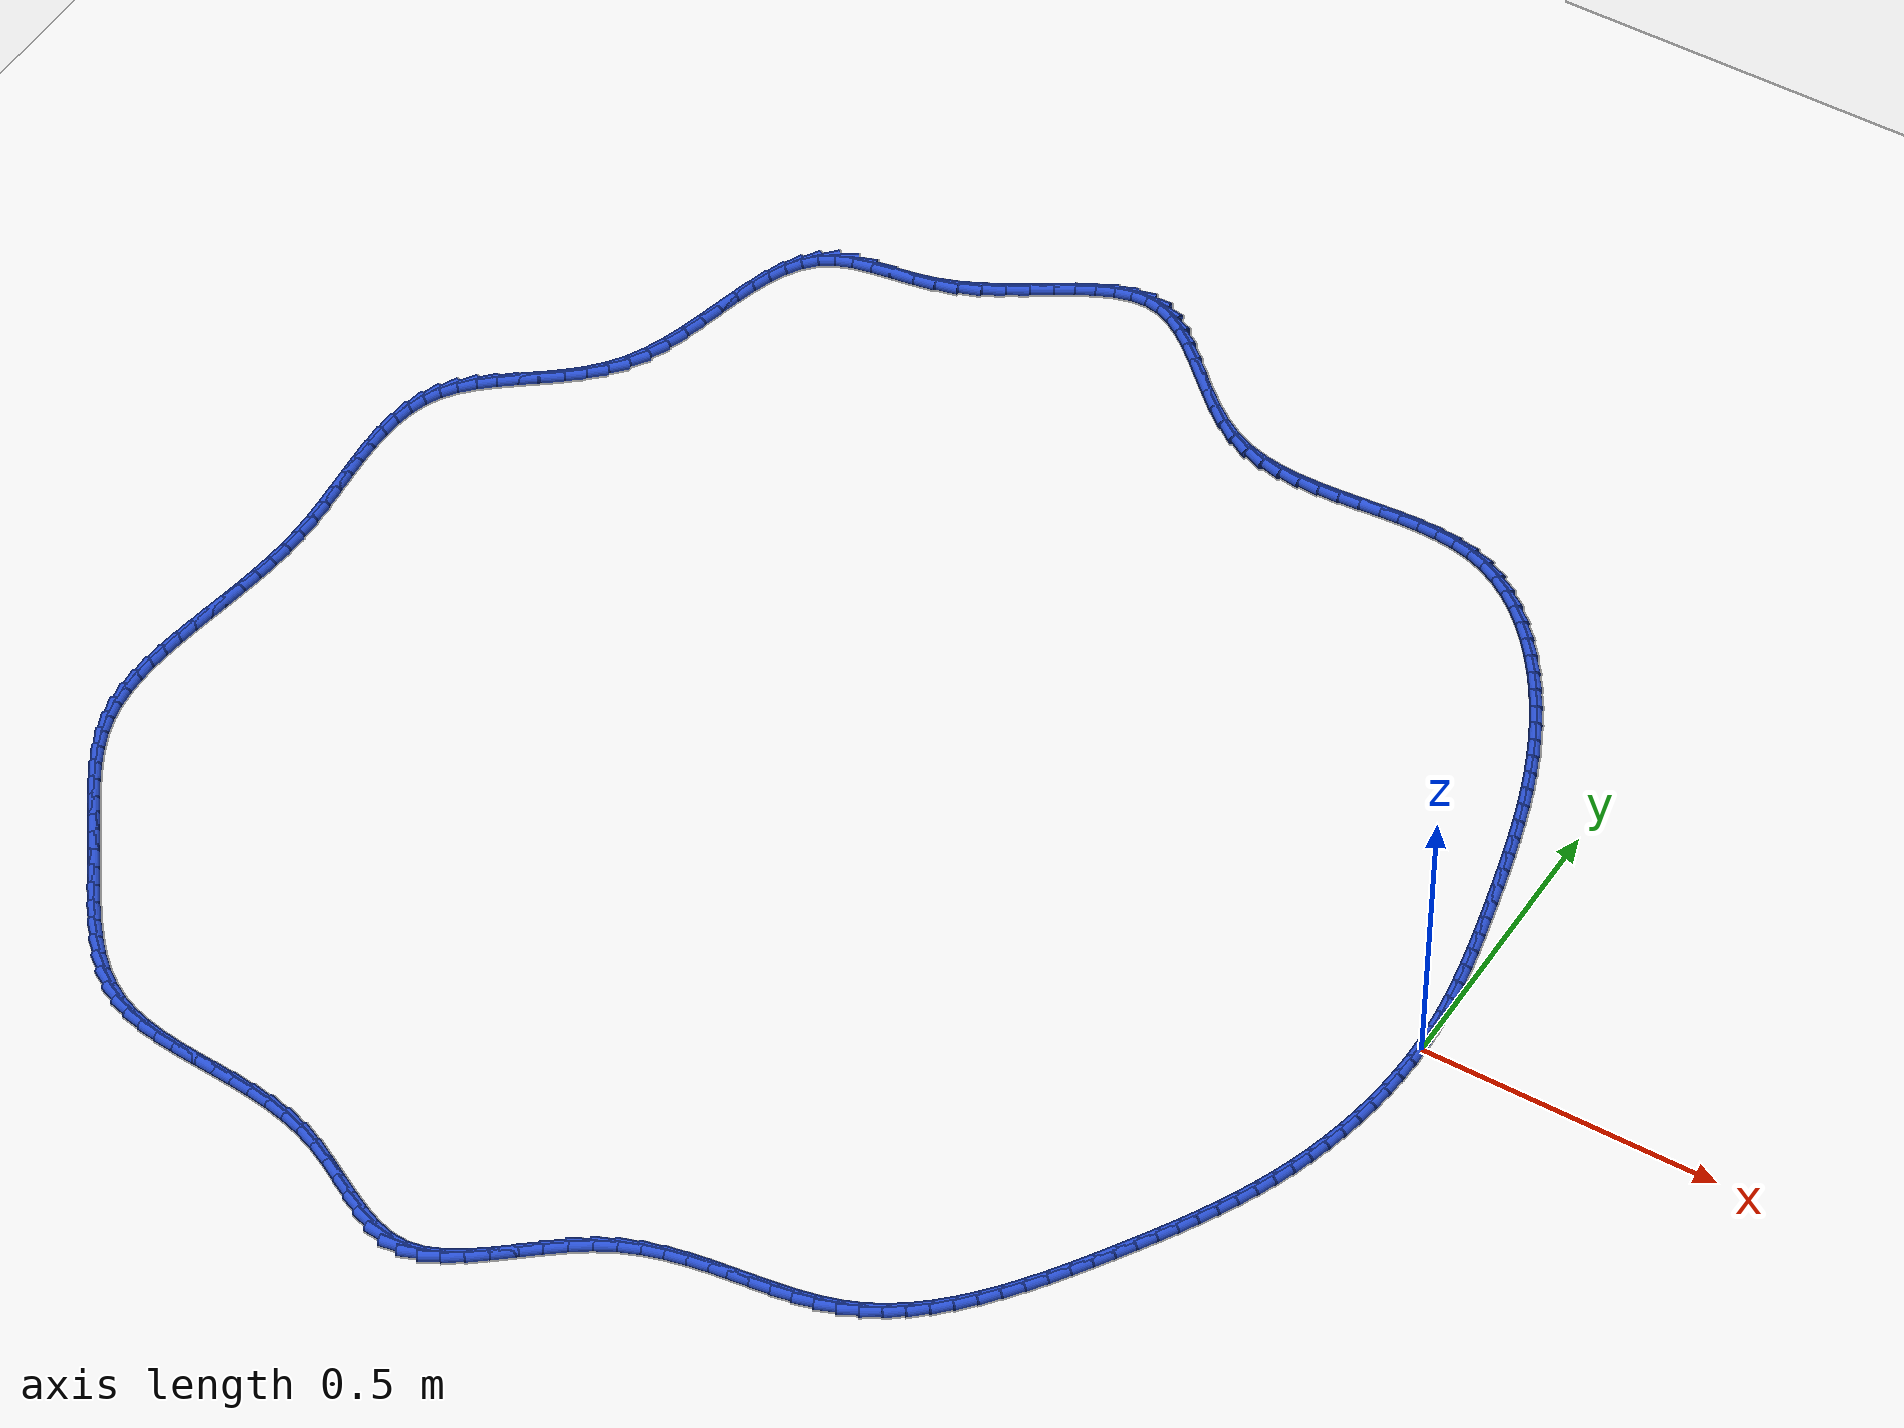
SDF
<sdf version="1.6">
 <world name="default">
  <light name="sun" type="directional">
   <pose>0 0 10 0 -0 0</pose>
   <diffuse>0.8 0.8 0.8 1</diffuse>
   <specular>0.2 0.2 0.2 1</specular>
   <attenuation>
    <range>1000</range>
    <constant>0.9</constant>
    <linear>0.01</linear>
    <quadratic>0.001</quadratic>
   </attenuation>
   <direction>-0.5 0.1 -0.9</direction>
  </light>
  <model name="ground_plane">
   <static>1</static>
   <link name="link">
    <collision name="collision">
     <geometry><plane><normal>0 0 1</normal><size>100 100</size></plane></geometry>
     <surface><friction><ode><mu>100</mu><mu2>50</mu2></ode></friction></surface>
    </collision>
    <visual name="visual">
     <cast_shadows>0</cast_shadows>
     <geometry><plane><normal>0 0 1</normal><size>100 100</size></plane></geometry>
     <material>
      <script><uri>file://media/materials/scripts/gazebo.material</uri><name>Gazebo/WhiteGlow</name></script>
     </material>
    </visual>
   </link>
  </model>
  <gravity>0 0 -9.8</gravity>
  <magnetic_field>6e-06 2.3e-05 -4.2e-05</magnetic_field>
  <atmosphere type="adiabatic"/>
  <physics name="default_physics" default="0" type="ode">
   <max_step_size>0.001</max_step_size>
   <real_time_factor>1</real_time_factor>
   <real_time_update_rate>1000</real_time_update_rate>
  </physics>
  <scene><ambient>0.4 0.4 0.4 1</ambient><background>0.7 0.7 0.7 1</background><shadows>1</shadows></scene>
  <spherical_coordinates>
   <surface_model>EARTH_WGS84</surface_model>
   <latitude_deg>0</latitude_deg>
   <longitude_deg>0</longitude_deg>
   <elevation>0</elevation>
   <heading_deg>0</heading_deg>
  </spherical_coordinates>
  <model name="line">
   <link name="link_0">
    <pose>6.938893903907228e-18 -1.1796119636642288e-16 0.01 0 1.57 -1.5264489816676594</pose>
    <collision name="collision">
     <geometry><cylinder><radius>0.01</radius><length>0.08</length></cylinder></geometry>
    </collision>
    <visual name="visual">
     <material>
      <script><name>Gazebo/Blue</name><uri>file://media/materials/scripts/gazebo.material</uri></script>
     </material>
     <geometry><cylinder><radius>0.01</radius><length>0.08</length></cylinder></geometry>
    </visual>
   </link>
   <link name="link_1">
    <pose>-0.0015467610386075527 0.03485545533591956 0.01 0 1.57 -1.4882659478826439</pose>
    <collision name="collision">
     <geometry><cylinder><radius>0.01</radius><length>0.08</length></cylinder></geometry>
    </collision>
    <visual name="visual">
     <material>
      <script><name>Gazebo/Blue</name><uri>file://media/materials/scripts/gazebo.material</uri></script>
     </material>
     <geometry><cylinder><radius>0.01</radius><length>0.08</length></cylinder></geometry>
    </visual>
   </link>
   <link name="link_2">
    <pose>-0.0044185333484661775 0.06957296484486963 0.01 0 1.57 -1.4543281719729082</pose>
    <collision name="collision">
     <geometry><cylinder><radius>0.01</radius><length>0.08</length></cylinder></geometry>
    </collision>
    <visual name="visual">
     <material>
      <script><name>Gazebo/Blue</name><uri>file://media/materials/scripts/gazebo.material</uri></script>
     </material>
     <geometry><cylinder><radius>0.01</radius><length>0.08</length></cylinder></geometry>
    </visual>
   </link>
   <link name="link_3">
    <pose>-0.008464915684399684 0.1041581234297182 0.01 0 1.57 -1.424693767751485</pose>
    <collision name="collision">
     <geometry><cylinder><radius>0.01</radius><length>0.08</length></cylinder></geometry>
    </collision>
    <visual name="visual">
     <material>
      <script><name>Gazebo/Blue</name><uri>file://media/materials/scripts/gazebo.material</uri></script>
     </material>
     <geometry><cylinder><radius>0.01</radius><length>0.08</length></cylinder></geometry>
    </visual>
   </link>
   <link name="link_4">
    <pose>-0.013535506801231889 0.13861652599333338 0.01 0 1.57 -1.3993772028632878</pose>
    <collision name="collision">
     <geometry><cylinder><radius>0.01</radius><length>0.08</length></cylinder></geometry>
    </collision>
    <visual name="visual">
     <material>
      <script><name>Gazebo/Blue</name><uri>file://media/materials/scripts/gazebo.material</uri></script>
     </material>
     <geometry><cylinder><radius>0.01</radius><length>0.08</length></cylinder></geometry>
    </visual>
   </link>
   <link name="link_5">
    <pose>-0.019479905453786604 0.17295376743858337 0.01 0 1.57 -1.378365679883654</pose>
    <collision name="collision">
     <geometry><cylinder><radius>0.01</radius><length>0.08</length></cylinder></geometry>
    </collision>
    <visual name="visual">
     <material>
      <script><name>Gazebo/Blue</name><uri>file://media/materials/scripts/gazebo.material</uri></script>
     </material>
     <geometry><cylinder><radius>0.01</radius><length>0.08</length></cylinder></geometry>
    </visual>
   </link>
   <link name="link_6">
    <pose>-0.02614771039688766 0.20717544266833637 0.01 0 1.57 -1.361633290367969</pose>
    <collision name="collision">
     <geometry><cylinder><radius>0.01</radius><length>0.08</length></cylinder></geometry>
    </collision>
    <visual name="visual">
     <material>
      <script><name>Gazebo/Blue</name><uri>file://media/materials/scripts/gazebo.material</uri></script>
     </material>
     <geometry><cylinder><radius>0.01</radius><length>0.08</length></cylinder></geometry>
    </visual>
   </link>
   <link name="link_7">
    <pose>-0.033388520385358854 0.24128714658546044 0.01 0 1.57 -1.3491526212590932</pose>
    <collision name="collision">
     <geometry><cylinder><radius>0.01</radius><length>0.08</length></cylinder></geometry>
    </collision>
    <visual name="visual">
     <material>
      <script><name>Gazebo/Blue</name><uri>file://media/materials/scripts/gazebo.material</uri></script>
     </material>
     <geometry><cylinder><radius>0.01</radius><length>0.08</length></cylinder></geometry>
    </visual>
   </link>
   <link name="link_8">
    <pose>-0.041051934174024 0.2752944740928237 0.01 0 1.57 -1.3409038187022755</pose>
    <collision name="collision">
     <geometry><cylinder><radius>0.01</radius><length>0.08</length></cylinder></geometry>
    </collision>
    <visual name="visual">
     <material>
      <script><name>Gazebo/Blue</name><uri>file://media/materials/scripts/gazebo.material</uri></script>
     </material>
     <geometry><cylinder><radius>0.01</radius><length>0.08</length></cylinder></geometry>
    </visual>
   </link>
   <link name="link_9">
    <pose>-0.04898755052486072 0.30920302009256817 0.01 0 1.57 -1.3356244483135322</pose>
    <collision name="collision">
     <geometry><cylinder><radius>0.01</radius><length>0.08</length></cylinder></geometry>
    </collision>
    <visual name="visual">
     <material>
      <script><name>Gazebo/Blue</name><uri>file://media/materials/scripts/gazebo.material</uri></script>
     </material>
     <geometry><cylinder><radius>0.01</radius><length>0.08</length></cylinder></geometry>
    </visual>
   </link>
   <link name="link_10">
    <pose>-0.057088827889704534 0.3430139272416276 0.01 0 1.57 -1.3283681049365337</pose>
    <collision name="collision">
     <geometry><cylinder><radius>0.01</radius><length>0.08</length></cylinder></geometry>
    </collision>
    <visual name="visual">
     <material>
      <script><name>Gazebo/Blue</name><uri>file://media/materials/scripts/gazebo.material</uri></script>
     </material>
     <geometry><cylinder><radius>0.01</radius><length>0.08</length></cylinder></geometry>
    </visual>
   </link>
   <link name="link_11">
    <pose>-0.06542179582705984 0.3767108203146784 0.01 0 1.57 -1.3179092680957762</pose>
    <collision name="collision">
     <geometry><cylinder><radius>0.01</radius><length>0.08</length></cylinder></geometry>
    </collision>
    <visual name="visual">
     <material>
      <script><name>Gazebo/Blue</name><uri>file://media/materials/scripts/gazebo.material</uri></script>
     </material>
     <geometry><cylinder><radius>0.01</radius><length>0.08</length></cylinder></geometry>
    </visual>
   </link>
   <link name="link_12">
    <pose>-0.07409492143907431 0.41027301620481044 0.01 0 1.57 -1.3042433775185882</pose>
    <collision name="collision">
     <geometry><cylinder><radius>0.01</radius><length>0.08</length></cylinder></geometry>
    </collision>
    <visual name="visual">
     <material>
      <script><name>Gazebo/Blue</name><uri>file://media/materials/scripts/gazebo.material</uri></script>
     </material>
     <geometry><cylinder><radius>0.01</radius><length>0.08</length></cylinder></geometry>
    </visual>
   </link>
   <link name="link_13">
    <pose>-0.08321667182789558 0.44367983180511394 0.01 0 1.57 -1.287375561786151</pose>
    <collision name="collision">
     <geometry><cylinder><radius>0.01</radius><length>0.08</length></cylinder></geometry>
    </collision>
    <visual name="visual">
     <material>
      <script><name>Gazebo/Blue</name><uri>file://media/materials/scripts/gazebo.material</uri></script>
     </material>
     <geometry><cylinder><radius>0.01</radius><length>0.08</length></cylinder></geometry>
    </visual>
   </link>
   <link name="link_14">
    <pose>-0.09289551409567123 0.4769105840086785 0.01 0 1.57 -1.2673248457521828</pose>
    <collision name="collision">
     <geometry><cylinder><radius>0.01</radius><length>0.08</length></cylinder></geometry>
    </collision>
    <visual name="visual">
     <material>
      <script><name>Gazebo/Blue</name><uri>file://media/materials/scripts/gazebo.material</uri></script>
     </material>
     <geometry><cylinder><radius>0.01</radius><length>0.08</length></cylinder></geometry>
    </visual>
   </link>
   <link name="link_15">
    <pose>-0.10323991534454893 0.5099445897085939 0.01 0 1.57 -1.2441291836012394</pose>
    <collision name="collision">
     <geometry><cylinder><radius>0.01</radius><length>0.08</length></cylinder></geometry>
    </collision>
    <visual name="visual">
     <material>
      <script><name>Gazebo/Blue</name><uri>file://media/materials/scripts/gazebo.material</uri></script>
     </material>
     <geometry><cylinder><radius>0.01</radius><length>0.08</length></cylinder></geometry>
    </visual>
   </link>
   <link name="link_16">
    <pose>-0.11435834267667627 0.5427611657979505 0.01 0 1.57 -1.2178511080925096</pose>
    <collision name="collision">
     <geometry><cylinder><radius>0.01</radius><length>0.08</length></cylinder></geometry>
    </collision>
    <visual name="visual">
     <material>
      <script><name>Gazebo/Blue</name><uri>file://media/materials/scripts/gazebo.material</uri></script>
     </material>
     <geometry><cylinder><radius>0.01</radius><length>0.08</length></cylinder></geometry>
    </visual>
   </link>
   <link name="link_17">
    <pose>-0.12635926319420096 0.5753396291698378 0.01 0 1.57 -1.1885836641636707</pose>
    <collision name="collision">
     <geometry><cylinder><radius>0.01</radius><length>0.08</length></cylinder></geometry>
    </collision>
    <visual name="visual">
     <material>
      <script><name>Gazebo/Blue</name><uri>file://media/materials/scripts/gazebo.material</uri></script>
     </material>
     <geometry><cylinder><radius>0.01</radius><length>0.08</length></cylinder></geometry>
    </visual>
   </link>
   <link name="link_18">
    <pose>-0.1393511439992705 0.6076592967173458 0.01 0 1.57 -1.15645615554688</pose>
    <collision name="collision">
     <geometry><cylinder><radius>0.01</radius><length>0.08</length></cylinder></geometry>
    </collision>
    <visual name="visual">
     <material>
      <script><name>Gazebo/Blue</name><uri>file://media/materials/scripts/gazebo.material</uri></script>
     </material>
     <geometry><cylinder><radius>0.01</radius><length>0.08</length></cylinder></geometry>
    </visual>
   </link>
   <link name="link_19">
    <pose>-0.15344245219403263 0.6396994853335645 0.01 0 1.57 -1.1216390971331887</pose>
    <collision name="collision">
     <geometry><cylinder><radius>0.01</radius><length>0.08</length></cylinder></geometry>
    </collision>
    <visual name="visual">
     <material>
      <script><name>Gazebo/Blue</name><uri>file://media/materials/scripts/gazebo.material</uri></script>
     </material>
     <geometry><cylinder><radius>0.01</radius><length>0.08</length></cylinder></geometry>
    </visual>
   </link>
   <link name="link_20">
    <pose>-0.16874165488063492 0.6714395119115835 0.01 0 1.57 -1.0843476659231157</pose>
    <collision name="collision">
     <geometry><cylinder><radius>0.01</radius><length>0.08</length></cylinder></geometry>
    </collision>
    <visual name="visual">
     <material>
      <script><name>Gazebo/Blue</name><uri>file://media/materials/scripts/gazebo.material</uri></script>
     </material>
     <geometry><cylinder><radius>0.01</radius><length>0.08</length></cylinder></geometry>
    </visual>
   </link>
   <link name="link_21">
    <pose>-0.185357219161225 0.7028586933444928 0.01 0 1.57 -1.0448429200627718</pose>
    <collision name="collision">
     <geometry><cylinder><radius>0.01</radius><length>0.08</length></cylinder></geometry>
    </collision>
    <visual name="visual">
     <material>
      <script><name>Gazebo/Blue</name><uri>file://media/materials/scripts/gazebo.material</uri></script>
     </material>
     <geometry><cylinder><radius>0.01</radius><length>0.08</length></cylinder></geometry>
    </visual>
   </link>
   <link name="link_22">
    <pose>-0.20339761213795055 0.7339363465253829 0.01 0 1.57 -1.0032738686366145</pose>
    <collision name="collision">
     <geometry><cylinder><radius>0.01</radius><length>0.08</length></cylinder></geometry>
    </collision>
    <visual name="visual">
     <material>
      <script><name>Gazebo/Blue</name><uri>file://media/materials/scripts/gazebo.material</uri></script>
     </material>
     <geometry><cylinder><radius>0.01</radius><length>0.08</length></cylinder></geometry>
    </visual>
   </link>
   <link name="link_23">
    <pose>-0.22296567955077506 0.7646323812961567 0.01 0 1.57 -0.9575760021214456</pose>
    <collision name="collision">
     <geometry><cylinder><radius>0.01</radius><length>0.08</length></cylinder></geometry>
    </collision>
    <visual name="visual">
     <material>
      <script><name>Gazebo/Blue</name><uri>file://media/materials/scripts/gazebo.material</uri></script>
     </material>
     <geometry><cylinder><radius>0.01</radius><length>0.08</length></cylinder></geometry>
    </visual>
   </link>
   <link name="link_24">
    <pose>-0.24409000756926694 0.7946503356022766 0.01 0 1.57 -0.9052711009615187</pose>
    <collision name="collision">
     <geometry><cylinder><radius>0.01</radius><length>0.08</length></cylinder></geometry>
    </collision>
    <visual name="visual">
     <material>
      <script><name>Gazebo/Blue</name><uri>file://media/materials/scripts/gazebo.material</uri></script>
     </material>
     <geometry><cylinder><radius>0.01</radius><length>0.08</length></cylinder></geometry>
    </visual>
   </link>
   <link name="link_25">
    <pose>-0.26674667125949636 0.8235124593597093 0.01 0 1.57 -0.844888720168654</pose>
    <collision name="collision">
     <geometry><cylinder><radius>0.01</radius><length>0.08</length></cylinder></geometry>
    </collision>
    <visual name="visual">
     <material>
      <script><name>Gazebo/Blue</name><uri>file://media/materials/scripts/gazebo.material</uri></script>
     </material>
     <geometry><cylinder><radius>0.01</radius><length>0.08</length></cylinder></geometry>
    </visual>
   </link>
   <link name="link_26">
    <pose>-0.29091063843119636 0.850737179820145 0.01 0 1.57 -0.7747488530673151</pose>
    <collision name="collision">
     <geometry><cylinder><radius>0.01</radius><length>0.08</length></cylinder></geometry>
    </collision>
    <visual name="visual">
     <material>
      <script><name>Gazebo/Blue</name><uri>file://media/materials/scripts/gazebo.material</uri></script>
     </material>
     <geometry><cylinder><radius>0.01</radius><length>0.08</length></cylinder></geometry>
    </visual>
   </link>
   <link name="link_27">
    <pose>-0.3165568768941006 0.8758429242352748 0.01 0 1.57 -0.6929711703929071</pose>
    <collision name="collision">
     <geometry><cylinder><radius>0.01</radius><length>0.08</length></cylinder></geometry>
    </collision>
    <visual name="visual">
     <material>
      <script><name>Gazebo/Blue</name><uri>file://media/materials/scripts/gazebo.material</uri></script>
     </material>
     <geometry><cylinder><radius>0.01</radius><length>0.08</length></cylinder></geometry>
    </visual>
   </link>
   <link name="link_28">
    <pose>-0.34366035445794235 0.8983481198567891 0.01 0 1.57 -0.5976272358362587</pose>
    <collision name="collision">
     <geometry><cylinder><radius>0.01</radius><length>0.08</length></cylinder></geometry>
    </collision>
    <visual name="visual">
     <material>
      <script><name>Gazebo/Blue</name><uri>file://media/materials/scripts/gazebo.material</uri></script>
     </material>
     <geometry><cylinder><radius>0.01</radius><length>0.08</length></cylinder></geometry>
    </visual>
   </link>
   <link name="link_29">
    <pose>-0.37219603893245484 0.9177711939363792 0.01 0 1.57 -0.4870890610263122</pose>
    <collision name="collision">
     <geometry><cylinder><radius>0.01</radius><length>0.08</length></cylinder></geometry>
    </collision>
    <visual name="visual">
     <material>
      <script><name>Gazebo/Blue</name><uri>file://media/materials/scripts/gazebo.material</uri></script>
     </material>
     <geometry><cylinder><radius>0.01</radius><length>0.08</length></cylinder></geometry>
    </visual>
   </link>
   <link name="link_30">
    <pose>-0.4021388981273718 0.9336305737257355 0.01 0 1.57 -0.3606638599698141</pose>
    <collision name="collision">
     <geometry><cylinder><radius>0.01</radius><length>0.08</length></cylinder></geometry>
    </collision>
    <visual name="visual">
     <material>
      <script><name>Gazebo/Blue</name><uri>file://media/materials/scripts/gazebo.material</uri></script>
     </material>
     <geometry><cylinder><radius>0.01</radius><length>0.08</length></cylinder></geometry>
    </visual>
   </link>
   <link name="link_31">
    <pose>-0.43346383465431504 0.9454451167405508 0.01 0 1.57 -0.2282722434890307</pose>
    <collision name="collision">
     <geometry><cylinder><radius>0.01</radius><length>0.08</length></cylinder></geometry>
    </collision>
    <visual name="visual">
     <material>
      <script><name>Gazebo/Blue</name><uri>file://media/materials/scripts/gazebo.material</uri></script>
     </material>
     <geometry><cylinder><radius>0.01</radius><length>0.08</length></cylinder></geometry>
    </visual>
   </link>
   <link name="link_32">
    <pose>-0.4661012301306202 0.9530274893304471 0.01 0 1.57 -0.11700415218146078</pose>
    <collision name="collision">
     <geometry><cylinder><radius>0.01</radius><length>0.08</length></cylinder></geometry>
    </collision>
    <visual name="visual">
     <material>
      <script><name>Gazebo/Blue</name><uri>file://media/materials/scripts/gazebo.material</uri></script>
     </material>
     <geometry><cylinder><radius>0.01</radius><length>0.08</length></cylinder></geometry>
    </visual>
   </link>
   <link name="link_33">
    <pose>-0.4998594675953271 0.956995466998728 0.01 0 1.57 -0.031951493490827425</pose>
    <collision name="collision">
     <geometry><cylinder><radius>0.01</radius><length>0.08</length></cylinder></geometry>
    </collision>
    <visual name="visual">
     <material>
      <script><name>Gazebo/Blue</name><uri>file://media/materials/scripts/gazebo.material</uri></script>
     </material>
     <geometry><cylinder><radius>0.01</radius><length>0.08</length></cylinder></geometry>
    </visual>
   </link>
   <link name="link_34">
    <pose>-0.5345262199089968 0.9581034985976825 0.01 0 1.57 0.028199047168971918</pose>
    <collision name="collision">
     <geometry><cylinder><radius>0.01</radius><length>0.08</length></cylinder></geometry>
    </collision>
    <visual name="visual">
     <material>
      <script><name>Gazebo/Blue</name><uri>file://media/materials/scripts/gazebo.material</uri></script>
     </material>
     <geometry><cylinder><radius>0.01</radius><length>0.08</length></cylinder></geometry>
    </visual>
   </link>
   <link name="link_35">
    <pose>-0.5698891599321906 0.9571060329795994 0.01 0 1.57 0.06542180699364927</pose>
    <collision name="collision">
     <geometry><cylinder><radius>0.01</radius><length>0.08</length></cylinder></geometry>
    </collision>
    <visual name="visual">
     <material>
      <script><name>Gazebo/Blue</name><uri>file://media/materials/scripts/gazebo.material</uri></script>
     </material>
     <geometry><cylinder><radius>0.01</radius><length>0.08</length></cylinder></geometry>
    </visual>
   </link>
   <link name="link_36">
    <pose>-0.6057359605254691 0.9547575189967683 0.01 0 1.57 0.0813606788135846</pose>
    <collision name="collision">
     <geometry><cylinder><radius>0.01</radius><length>0.08</length></cylinder></geometry>
    </collision>
    <visual name="visual">
     <material>
      <script><name>Gazebo/Blue</name><uri>file://media/materials/scripts/gazebo.material</uri></script>
     </material>
     <geometry><cylinder><radius>0.01</radius><length>0.08</length></cylinder></geometry>
    </visual>
   </link>
   <link name="link_37">
    <pose>-0.6418542945493942 0.9518124055014784 0.01 0 1.57 0.07689214971873724</pose>
    <collision name="collision">
     <geometry><cylinder><radius>0.01</radius><length>0.08</length></cylinder></geometry>
    </collision>
    <visual name="visual">
     <material>
      <script><name>Gazebo/Blue</name><uri>file://media/materials/scripts/gazebo.material</uri></script>
     </material>
     <geometry><cylinder><radius>0.01</radius><length>0.08</length></cylinder></geometry>
    </visual>
   </link>
   <link name="link_38">
    <pose>-0.6780318348645269 0.9490251413460182 0.01 0 1.57 0.05200016284586164</pose>
    <collision name="collision">
     <geometry><cylinder><radius>0.01</radius><length>0.08</length></cylinder></geometry>
    </collision>
    <visual name="visual">
     <material>
      <script><name>Gazebo/Blue</name><uri>file://media/materials/scripts/gazebo.material</uri></script>
     </material>
     <geometry><cylinder><radius>0.01</radius><length>0.08</length></cylinder></geometry>
    </visual>
   </link>
   <link name="link_39">
    <pose>-0.7140562543314283 0.9471501753826779 0.01 0 1.57 0.005839107070951549</pose>
    <collision name="collision">
     <geometry><cylinder><radius>0.01</radius><length>0.08</length></cylinder></geometry>
    </collision>
    <visual name="visual">
     <material>
      <script><name>Gazebo/Blue</name><uri>file://media/materials/scripts/gazebo.material</uri></script>
     </material>
     <geometry><cylinder><radius>0.01</radius><length>0.08</length></cylinder></geometry>
    </visual>
   </link>
   <link name="link_40">
    <pose>-0.749715225810659 0.9469419564637453 0.01 0 1.57 -0.06299809701540393</pose>
    <collision name="collision">
     <geometry><cylinder><radius>0.01</radius><length>0.08</length></cylinder></geometry>
    </collision>
    <visual name="visual">
     <material>
      <script><name>Gazebo/Blue</name><uri>file://media/materials/scripts/gazebo.material</uri></script>
     </material>
     <geometry><cylinder><radius>0.01</radius><length>0.08</length></cylinder></geometry>
    </visual>
   </link>
   <link name="link_41">
    <pose>-0.7847964221627811 0.9491549334415109 0.01 0 1.57 -0.1558688055210482</pose>
    <collision name="collision">
     <geometry><cylinder><radius>0.01</radius><length>0.08</length></cylinder></geometry>
    </collision>
    <visual name="visual">
     <material>
      <script><name>Gazebo/Blue</name><uri>file://media/materials/scripts/gazebo.material</uri></script>
     </material>
     <geometry><cylinder><radius>0.01</radius><length>0.08</length></cylinder></geometry>
    </visual>
   </link>
   <link name="link_42">
    <pose>-0.8190875162483549 0.9545435551682628 0.01 0 1.57 -0.2729499034922618</pose>
    <collision name="collision">
     <geometry><cylinder><radius>0.01</radius><length>0.08</length></cylinder></geometry>
    </collision>
    <visual name="visual">
     <material>
      <script><name>Gazebo/Blue</name><uri>file://media/materials/scripts/gazebo.material</uri></script>
     </material>
     <geometry><cylinder><radius>0.01</radius><length>0.08</length></cylinder></geometry>
    </visual>
   </link>
   <link name="link_43">
    <pose>-0.852376180927942 0.9638622704962909 0.01 0 1.57 -0.41161540998264795</pose>
    <collision name="collision">
     <geometry><cylinder><radius>0.01</radius><length>0.08</length></cylinder></geometry>
    </collision>
    <visual name="visual">
     <material>
      <script><name>Gazebo/Blue</name><uri>file://media/materials/scripts/gazebo.material</uri></script>
     </material>
     <geometry><cylinder><radius>0.01</radius><length>0.08</length></cylinder></geometry>
    </visual>
   </link>
   <link name="link_44">
    <pose>-0.8844503273385146 0.9778643392958822 0.01 0 1.57 -0.5514213558929584</pose>
    <collision name="collision">
     <geometry><cylinder><radius>0.01</radius><length>0.08</length></cylinder></geometry>
    </collision>
    <visual name="visual">
     <material>
      <script><name>Gazebo/Blue</name><uri>file://media/materials/scripts/gazebo.material</uri></script>
     </material>
     <geometry><cylinder><radius>0.01</radius><length>0.08</length></cylinder></geometry>
    </visual>
   </link>
   <link name="link_45">
    <pose>-0.9152028673650509 0.996779075323483 0.01 0 1.57 -0.654606473054333</pose>
    <collision name="collision">
     <geometry><cylinder><radius>0.01</radius><length>0.08</length></cylinder></geometry>
    </collision>
    <visual name="visual">
     <material>
      <script><name>Gazebo/Blue</name><uri>file://media/materials/scripts/gazebo.material</uri></script>
     </material>
     <geometry><cylinder><radius>0.01</radius><length>0.08</length></cylinder></geometry>
    </visual>
   </link>
   <link name="link_46">
    <pose>-0.9447960531660089 1.019491803913828 0.01 0 1.57 -0.721291385311221</pose>
    <collision name="collision">
     <geometry><cylinder><radius>0.01</radius><length>0.08</length></cylinder></geometry>
    </collision>
    <visual name="visual">
     <material>
      <script><name>Gazebo/Blue</name><uri>file://media/materials/scripts/gazebo.material</uri></script>
     </material>
     <geometry><cylinder><radius>0.01</radius><length>0.08</length></cylinder></geometry>
    </visual>
   </link>
   <link name="link_47">
    <pose>-0.9734347195260533 1.0446753661866195 0.01 0 1.57 -0.7566002702176771</pose>
    <collision name="collision">
     <geometry><cylinder><radius>0.01</radius><length>0.08</length></cylinder></geometry>
    </collision>
    <visual name="visual">
     <material>
      <script><name>Gazebo/Blue</name><uri>file://media/materials/scripts/gazebo.material</uri></script>
     </material>
     <geometry><cylinder><radius>0.01</radius><length>0.08</length></cylinder></geometry>
    </visual>
   </link>
   <link name="link_48">
    <pose>-1.001323701229849 1.0710026032615596 0.01 0 1.57 -0.762959860257623</pose>
    <collision name="collision">
     <geometry><cylinder><radius>0.01</radius><length>0.08</length></cylinder></geometry>
    </collision>
    <visual name="visual">
     <material>
      <script><name>Gazebo/Blue</name><uri>file://media/materials/scripts/gazebo.material</uri></script>
     </material>
     <geometry><cylinder><radius>0.01</radius><length>0.08</length></cylinder></geometry>
    </visual>
   </link>
   <link name="link_49">
    <pose>-1.028667833062061 1.0971463562583508 0.01 0 1.57 -0.7395137759778166</pose>
    <collision name="collision">
     <geometry><cylinder><radius>0.01</radius><length>0.08</length></cylinder></geometry>
    </collision>
    <visual name="visual">
     <material>
      <script><name>Gazebo/Blue</name><uri>file://media/materials/scripts/gazebo.material</uri></script>
     </material>
     <geometry><cylinder><radius>0.01</radius><length>0.08</length></cylinder></geometry>
    </visual>
   </link>
   <link name="link_50">
    <pose>-1.0556719498073537 1.1217794662966944 0.01 0 1.57 -0.6815156451526158</pose>
    <collision name="collision">
     <geometry><cylinder><radius>0.01</radius><length>0.08</length></cylinder></geometry>
    </collision>
    <visual name="visual">
     <material>
      <script><name>Gazebo/Blue</name><uri>file://media/materials/scripts/gazebo.material</uri></script>
     </material>
     <geometry><cylinder><radius>0.01</radius><length>0.08</length></cylinder></geometry>
    </visual>
   </link>
   <link name="link_51">
    <pose>-1.0825408862503916 1.1435747744962932 0.01 0 1.57 -0.5795072064655616</pose>
    <collision name="collision">
     <geometry><cylinder><radius>0.01</radius><length>0.08</length></cylinder></geometry>
    </collision>
    <visual name="visual">
     <material>
      <script><name>Gazebo/Blue</name><uri>file://media/materials/scripts/gazebo.material</uri></script>
     </material>
     <geometry><cylinder><radius>0.01</radius><length>0.08</length></cylinder></geometry>
    </visual>
   </link>
   <link name="link_52">
    <pose>-1.1094794771758394 1.1612051219768484 0.01 0 1.57 -0.4195591477306667</pose>
    <collision name="collision">
     <geometry><cylinder><radius>0.01</radius><length>0.08</length></cylinder></geometry>
    </collision>
    <visual name="visual">
     <material>
      <script><name>Gazebo/Blue</name><uri>file://media/materials/scripts/gazebo.material</uri></script>
     </material>
     <geometry><cylinder><radius>0.01</radius><length>0.08</length></cylinder></geometry>
    </visual>
   </link>
   <link name="link_53">
    <pose>-1.1366925573683622 1.173343349858063 0.01 0 1.57 -0.1902161290354234</pose>
    <collision name="collision">
     <geometry><cylinder><radius>0.01</radius><length>0.08</length></cylinder></geometry>
    </collision>
    <visual name="visual">
     <material>
      <script><name>Gazebo/Blue</name><uri>file://media/materials/scripts/gazebo.material</uri></script>
     </material>
     <geometry><cylinder><radius>0.01</radius><length>0.08</length></cylinder></geometry>
    </visual>
   </link>
   <link name="link_54">
    <pose>-1.1643841514576756 1.1786751993157139 0.01 0 1.57 0.06627865184186088</pose>
    <collision name="collision">
     <geometry><cylinder><radius>0.01</radius><length>0.08</length></cylinder></geometry>
    </collision>
    <visual name="visual">
     <material>
      <script><name>Gazebo/Blue</name><uri>file://media/materials/scripts/gazebo.material</uri></script>
     </material>
     <geometry><cylinder><radius>0.01</radius><length>0.08</length></cylinder></geometry>
    </visual>
   </link>
   <link name="link_55">
    <pose>-1.1927011828365597 1.1767956316196888 0.01 0 1.57 0.26930037695229053</pose>
    <collision name="collision">
     <geometry><cylinder><radius>0.01</radius><length>0.08</length></cylinder></geometry>
    </collision>
    <visual name="visual">
     <material>
      <script><name>Gazebo/Blue</name><uri>file://media/materials/scripts/gazebo.material</uri></script>
     </material>
     <geometry><cylinder><radius>0.01</radius><length>0.08</length></cylinder></geometry>
    </visual>
   </link>
   <link name="link_56">
    <pose>-1.2216968055424162 1.168792692720583 0.01 0 1.57 0.4095146152992243</pose>
    <collision name="collision">
     <geometry><cylinder><radius>0.01</radius><length>0.08</length></cylinder></geometry>
    </collision>
    <visual name="visual">
     <material>
      <script><name>Gazebo/Blue</name><uri>file://media/materials/scripts/gazebo.material</uri></script>
     </material>
     <geometry><cylinder><radius>0.01</radius><length>0.08</length></cylinder></geometry>
    </visual>
   </link>
   <link name="link_57">
    <pose>-1.2514154593893008 1.155893184704535 0.01 0 1.57 0.49784079139923687</pose>
    <collision name="collision">
     <geometry><cylinder><radius>0.01</radius><length>0.08</length></cylinder></geometry>
    </collision>
    <visual name="visual">
     <material>
      <script><name>Gazebo/Blue</name><uri>file://media/materials/scripts/gazebo.material</uri></script>
     </material>
     <geometry><cylinder><radius>0.01</radius><length>0.08</length></cylinder></geometry>
    </visual>
   </link>
   <link name="link_58">
    <pose>-1.281901584191268 1.1393239096576835 0.01 0 1.57 0.5458852361291224</pose>
    <collision name="collision">
     <geometry><cylinder><radius>0.01</radius><length>0.08</length></cylinder></geometry>
    </collision>
    <visual name="visual">
     <material>
      <script><name>Gazebo/Blue</name><uri>file://media/materials/scripts/gazebo.material</uri></script>
     </material>
     <geometry><cylinder><radius>0.01</radius><length>0.08</length></cylinder></geometry>
    </visual>
   </link>
   <link name="link_59">
    <pose>-1.3131996197623732 1.1203116696661655 0.01 0 1.57 0.561543948157743</pose>
    <collision name="collision">
     <geometry><cylinder><radius>0.01</radius><length>0.08</length></cylinder></geometry>
    </collision>
    <visual name="visual">
     <material>
      <script><name>Gazebo/Blue</name><uri>file://media/materials/scripts/gazebo.material</uri></script>
     </material>
     <geometry><cylinder><radius>0.01</radius><length>0.08</length></cylinder></geometry>
    </visual>
   </link>
   <link name="link_60">
    <pose>-1.3453540059166718 1.10008326681612 0.01 0 1.57 0.5489320883970408</pose>
    <collision name="collision">
     <geometry><cylinder><radius>0.01</radius><length>0.08</length></cylinder></geometry>
    </collision>
    <visual name="visual">
     <material>
      <script><name>Gazebo/Blue</name><uri>file://media/materials/scripts/gazebo.material</uri></script>
     </material>
     <geometry><cylinder><radius>0.01</radius><length>0.08</length></cylinder></geometry>
    </visual>
   </link>
   <link name="link_61">
    <pose>-1.378409182468218 1.0798655031936848 0.01 0 1.57 0.5091460350019192</pose>
    <collision name="collision">
     <geometry><cylinder><radius>0.01</radius><length>0.08</length></cylinder></geometry>
    </collision>
    <visual name="visual">
     <material>
      <script><name>Gazebo/Blue</name><uri>file://media/materials/scripts/gazebo.material</uri></script>
     </material>
     <geometry><cylinder><radius>0.01</radius><length>0.08</length></cylinder></geometry>
    </visual>
   </link>
   <link name="link_62">
    <pose>-1.4124095892310684 1.060885180884998 0.01 0 1.57 0.4410155865946592</pose>
    <collision name="collision">
     <geometry><cylinder><radius>0.01</radius><length>0.08</length></cylinder></geometry>
    </collision>
    <visual name="visual">
     <material>
      <script><name>Gazebo/Blue</name><uri>file://media/materials/scripts/gazebo.material</uri></script>
     </material>
     <geometry><cylinder><radius>0.01</radius><length>0.08</length></cylinder></geometry>
    </visual>
   </link>
   <link name="link_63">
    <pose>-1.4473996660192763 1.0443691019761978 0.01 0 1.57 0.3420258116617876</pose>
    <collision name="collision">
     <geometry><cylinder><radius>0.01</radius><length>0.08</length></cylinder></geometry>
    </collision>
    <visual name="visual">
     <material>
      <script><name>Gazebo/Blue</name><uri>file://media/materials/scripts/gazebo.material</uri></script>
     </material>
     <geometry><cylinder><radius>0.01</radius><length>0.08</length></cylinder></geometry>
    </visual>
   </link>
   <link name="link_64">
    <pose>-1.483423780895928 1.0315438752486528 0.01 0 1.57 0.2289081516052746</pose>
    <collision name="collision">
     <geometry><cylinder><radius>0.01</radius><length>0.08</length></cylinder></geometry>
    </collision>
    <visual name="visual">
     <material>
      <script><name>Gazebo/Blue</name><uri>file://media/materials/scripts/gazebo.material</uri></script>
     </material>
     <geometry><cylinder><radius>0.01</radius><length>0.08</length></cylinder></geometry>
    </visual>
   </link>
   <link name="link_65">
    <pose>-1.5202745772567352 1.0229579363702708 0.01 0 1.57 0.16216338841943173</pose>
    <collision name="collision">
     <geometry><cylinder><radius>0.01</radius><length>0.08</length></cylinder></geometry>
    </collision>
    <visual name="visual">
     <material>
      <script><name>Gazebo/Blue</name><uri>file://media/materials/scripts/gazebo.material</uri></script>
     </material>
     <geometry><cylinder><radius>0.01</radius><length>0.08</length></cylinder></geometry>
    </visual>
   </link>
   <link name="link_66">
    <pose>-1.5569286961549798 1.0169613236292652 0.01 0 1.57 0.1547512399086623</pose>
    <collision name="collision">
     <geometry><cylinder><radius>0.01</radius><length>0.08</length></cylinder></geometry>
    </collision>
    <visual name="visual">
     <material>
      <script><name>Gazebo/Blue</name><uri>file://media/materials/scripts/gazebo.material</uri></script>
     </material>
     <geometry><cylinder><radius>0.01</radius><length>0.08</length></cylinder></geometry>
    </visual>
   </link>
   <link name="link_67">
    <pose>-1.5921977265284961 1.011459407303419 0.01 0 1.57 0.2138891137005627</pose>
    <collision name="collision">
     <geometry><cylinder><radius>0.01</radius><length>0.08</length></cylinder></geometry>
    </collision>
    <visual name="visual">
     <material>
      <script><name>Gazebo/Blue</name><uri>file://media/materials/scripts/gazebo.material</uri></script>
     </material>
     <geometry><cylinder><radius>0.01</radius><length>0.08</length></cylinder></geometry>
    </visual>
   </link>
   <link name="link_68">
    <pose>-1.624893257315119 1.004357557670516 0.01 0 1.57 0.3571426794130867</pose>
    <collision name="collision">
     <geometry><cylinder><radius>0.01</radius><length>0.08</length></cylinder></geometry>
    </collision>
    <visual name="visual">
     <material>
      <script><name>Gazebo/Blue</name><uri>file://media/materials/scripts/gazebo.material</uri></script>
     </material>
     <geometry><cylinder><radius>0.01</radius><length>0.08</length></cylinder></geometry>
    </visual>
   </link>
   <link name="link_69">
    <pose>-1.6538268774526825 0.9935611450083397 0.01 0 1.57 0.5926429524447806</pose>
    <collision name="collision">
     <geometry><cylinder><radius>0.01</radius><length>0.08</length></cylinder></geometry>
    </collision>
    <visual name="visual">
     <material>
      <script><name>Gazebo/Blue</name><uri>file://media/materials/scripts/gazebo.material</uri></script>
     </material>
     <geometry><cylinder><radius>0.01</radius><length>0.08</length></cylinder></geometry>
    </visual>
   </link>
   <link name="link_70">
    <pose>-1.678013033209185 0.9772744237562716 0.01 0 1.57 0.8335422051172552</pose>
    <collision name="collision">
     <geometry><cylinder><radius>0.01</radius><length>0.08</length></cylinder></geometry>
    </collision>
    <visual name="visual">
     <material>
      <script><name>Gazebo/Blue</name><uri>file://media/materials/scripts/gazebo.material</uri></script>
     </material>
     <geometry><cylinder><radius>0.01</radius><length>0.08</length></cylinder></geometry>
    </visual>
   </link>
   <link name="link_71">
    <pose>-1.6977290541005878 0.9555623442450272 0.01 0 1.57 1.0249874786317912</pose>
    <collision name="collision">
     <geometry><cylinder><radius>0.01</radius><length>0.08</length></cylinder></geometry>
    </collision>
    <visual name="visual">
     <material>
      <script><name>Gazebo/Blue</name><uri>file://media/materials/scripts/gazebo.material</uri></script>
     </material>
     <geometry><cylinder><radius>0.01</radius><length>0.08</length></cylinder></geometry>
    </visual>
   </link>
   <link name="link_72">
    <pose>-1.71373745176025 0.9292047101964361 0.01 0 1.57 1.1627765604413665</pose>
    <collision name="collision">
     <geometry><cylinder><radius>0.01</radius><length>0.08</length></cylinder></geometry>
    </collision>
    <visual name="visual">
     <material>
      <script><name>Gazebo/Blue</name><uri>file://media/materials/scripts/gazebo.material</uri></script>
     </material>
     <geometry><cylinder><radius>0.01</radius><length>0.08</length></cylinder></geometry>
    </visual>
   </link>
   <link name="link_73">
    <pose>-1.7268017434008651 0.8989828069240285 0.01 0 1.57 1.254946320624883</pose>
    <collision name="collision">
     <geometry><cylinder><radius>0.01</radius><length>0.08</length></cylinder></geometry>
    </collision>
    <visual name="visual">
     <material>
      <script><name>Gazebo/Blue</name><uri>file://media/materials/scripts/gazebo.material</uri></script>
     </material>
     <geometry><cylinder><radius>0.01</radius><length>0.08</length></cylinder></geometry>
    </visual>
   </link>
   <link name="link_74">
    <pose>-1.737685446235127 0.8656779197413339 0.01 0 1.57 1.3109402642755787</pose>
    <collision name="collision">
     <geometry><cylinder><radius>0.01</radius><length>0.08</length></cylinder></geometry>
    </collision>
    <visual name="visual">
     <material>
      <script><name>Gazebo/Blue</name><uri>file://media/materials/scripts/gazebo.material</uri></script>
     </material>
     <geometry><cylinder><radius>0.01</radius><length>0.08</length></cylinder></geometry>
    </visual>
   </link>
   <link name="link_75">
    <pose>-1.7471520774757299 0.830071333961883 0.01 0 1.57 1.3377334411269795</pose>
    <collision name="collision">
     <geometry><cylinder><radius>0.01</radius><length>0.08</length></cylinder></geometry>
    </collision>
    <visual name="visual">
     <material>
      <script><name>Gazebo/Blue</name><uri>file://media/materials/scripts/gazebo.material</uri></script>
     </material>
     <geometry><cylinder><radius>0.01</radius><length>0.08</length></cylinder></geometry>
    </visual>
   </link>
   <link name="link_76">
    <pose>-1.7559651543353678 0.7929443348992055 0.01 0 1.57 1.3393713040512603</pose>
    <collision name="collision">
     <geometry><cylinder><radius>0.01</radius><length>0.08</length></cylinder></geometry>
    </collision>
    <visual name="visual">
     <material>
      <script><name>Gazebo/Blue</name><uri>file://media/materials/scripts/gazebo.material</uri></script>
     </material>
     <geometry><cylinder><radius>0.01</radius><length>0.08</length></cylinder></geometry>
    </visual>
   </link>
   <link name="link_77">
    <pose>-1.7648881940267336 0.7550782078668307 0.01 0 1.57 1.317362411852407</pose>
    <collision name="collision">
     <geometry><cylinder><radius>0.01</radius><length>0.08</length></cylinder></geometry>
    </collision>
    <visual name="visual">
     <material>
      <script><name>Gazebo/Blue</name><uri>file://media/materials/scripts/gazebo.material</uri></script>
     </material>
     <geometry><cylinder><radius>0.01</radius><length>0.08</length></cylinder></geometry>
    </visual>
   </link>
   <link name="link_78">
    <pose>-1.774684713762523 0.7172542381782895 0.01 0 1.57 1.2710945031337908</pose>
    <collision name="collision">
     <geometry><cylinder><radius>0.01</radius><length>0.08</length></cylinder></geometry>
    </collision>
    <visual name="visual">
     <material>
      <script><name>Gazebo/Blue</name><uri>file://media/materials/scripts/gazebo.material</uri></script>
     </material>
     <geometry><cylinder><radius>0.01</radius><length>0.08</length></cylinder></geometry>
    </visual>
   </link>
   <link name="link_79">
    <pose>-1.7861182307554286 0.6802537111471112 0.01 0 1.57 1.1982128922027853</pose>
    <collision name="collision">
     <geometry><cylinder><radius>0.01</radius><length>0.08</length></cylinder></geometry>
    </collision>
    <visual name="visual">
     <material>
      <script><name>Gazebo/Blue</name><uri>file://media/materials/scripts/gazebo.material</uri></script>
     </material>
     <geometry><cylinder><radius>0.01</radius><length>0.08</length></cylinder></geometry>
    </visual>
   </link>
   <link name="link_80">
    <pose>-1.7999522622181447 0.6448579120868259 0.01 0 1.57 1.095268180467855</pose>
    <collision name="collision">
     <geometry><cylinder><radius>0.01</radius><length>0.08</length></cylinder></geometry>
    </collision>
    <visual name="visual">
     <material>
      <script><name>Gazebo/Blue</name><uri>file://media/materials/scripts/gazebo.material</uri></script>
     </material>
     <geometry><cylinder><radius>0.01</radius><length>0.08</length></cylinder></geometry>
    </visual>
   </link>
   <link name="link_81">
    <pose>-1.8169503253633654 0.6118481263109639 0.01 0 1.57 0.9611433987964741</pose>
    <collision name="collision">
     <geometry><cylinder><radius>0.01</radius><length>0.08</length></cylinder></geometry>
    </collision>
    <visual name="visual">
     <material>
      <script><name>Gazebo/Blue</name><uri>file://media/materials/scripts/gazebo.material</uri></script>
     </material>
     <geometry><cylinder><radius>0.01</radius><length>0.08</length></cylinder></geometry>
    </visual>
   </link>
   <link name="link_82">
    <pose>-1.8378221503051677 0.5819630261401841 0.01 0 1.57 0.8306837052279497</pose>
    <collision name="collision">
     <geometry><cylinder><radius>0.01</radius><length>0.08</length></cylinder></geometry>
    </collision>
    <visual name="visual">
     <material>
      <script><name>Gazebo/Blue</name><uri>file://media/materials/scripts/gazebo.material</uri></script>
     </material>
     <geometry><cylinder><radius>0.01</radius><length>0.08</length></cylinder></geometry>
    </visual>
   </link>
   <link name="link_83">
    <pose>-1.862297077558162 0.5551645672458527 0.01 0 1.57 0.736324770996962</pose>
    <collision name="collision">
     <geometry><cylinder><radius>0.01</radius><length>0.08</length></cylinder></geometry>
    </collision>
    <visual name="visual">
     <material>
      <script><name>Gazebo/Blue</name><uri>file://media/materials/scripts/gazebo.material</uri></script>
     </material>
     <geometry><cylinder><radius>0.01</radius><length>0.08</length></cylinder></geometry>
    </visual>
   </link>
   <link name="link_84">
    <pose>-1.8892484745143812 0.5307365579831942 0.01 0 1.57 0.6785800644903094</pose>
    <collision name="collision">
     <geometry><cylinder><radius>0.01</radius><length>0.08</length></cylinder></geometry>
    </collision>
    <visual name="visual">
     <material>
      <script><name>Gazebo/Blue</name><uri>file://media/materials/scripts/gazebo.material</uri></script>
     </material>
     <geometry><cylinder><radius>0.01</radius><length>0.08</length></cylinder></geometry>
    </visual>
   </link>
   <link name="link_85">
    <pose>-1.9175209485142364 0.5079400214688465 0.01 0 1.57 0.6563256951702247</pose>
    <collision name="collision">
     <geometry><cylinder><radius>0.01</radius><length>0.08</length></cylinder></geometry>
    </collision>
    <visual name="visual">
     <material>
      <script><name>Gazebo/Blue</name><uri>file://media/materials/scripts/gazebo.material</uri></script>
     </material>
     <geometry><cylinder><radius>0.01</radius><length>0.08</length></cylinder></geometry>
    </visual>
   </link>
   <link name="link_86">
    <pose>-1.945959106898136 0.4860359808194489 0.01 0 1.57 0.6700978612645064</pose>
    <collision name="collision">
     <geometry><cylinder><radius>0.01</radius><length>0.08</length></cylinder></geometry>
    </collision>
    <visual name="visual">
     <material>
      <script><name>Gazebo/Blue</name><uri>file://media/materials/scripts/gazebo.material</uri></script>
     </material>
     <geometry><cylinder><radius>0.01</radius><length>0.08</length></cylinder></geometry>
    </visual>
   </link>
   <link name="link_87">
    <pose>-1.9734075570064906 0.46428545915164 0.01 0 1.57 0.7231902992890544</pose>
    <collision name="collision">
     <geometry><cylinder><radius>0.01</radius><length>0.08</length></cylinder></geometry>
    </collision>
    <visual name="visual">
     <material>
      <script><name>Gazebo/Blue</name><uri>file://media/materials/scripts/gazebo.material</uri></script>
     </material>
     <geometry><cylinder><radius>0.01</radius><length>0.08</length></cylinder></geometry>
    </visual>
   </link>
   <link name="link_88">
    <pose>-1.9987109061797115 0.4419494795820591 0.01 0 1.57 0.8216818399691129</pose>
    <collision name="collision">
     <geometry><cylinder><radius>0.01</radius><length>0.08</length></cylinder></geometry>
    </collision>
    <visual name="visual">
     <material>
      <script><name>Gazebo/Blue</name><uri>file://media/materials/scripts/gazebo.material</uri></script>
     </material>
     <geometry><cylinder><radius>0.01</radius><length>0.08</length></cylinder></geometry>
    </visual>
   </link>
   <link name="link_89">
    <pose>-2.0207137617582074 0.4182890652273446 0.01 0 1.57 0.9715307264322418</pose>
    <collision name="collision">
     <geometry><cylinder><radius>0.01</radius><length>0.08</length></cylinder></geometry>
    </collision>
    <visual name="visual">
     <material>
      <script><name>Gazebo/Blue</name><uri>file://media/materials/scripts/gazebo.material</uri></script>
     </material>
     <geometry><cylinder><radius>0.01</radius><length>0.08</length></cylinder></geometry>
    </visual>
   </link>
   <link name="link_90">
    <pose>-2.0382780981422046 0.3925748432527212 0.01 0 1.57 1.1456842950751396</pose>
    <collision name="collision">
     <geometry><cylinder><radius>0.01</radius><length>0.08</length></cylinder></geometry>
    </collision>
    <visual name="visual">
     <material>
      <script><name>Gazebo/Blue</name><uri>file://media/materials/scripts/gazebo.material</uri></script>
     </material>
     <geometry><cylinder><radius>0.01</radius><length>0.08</length></cylinder></geometry>
    </visual>
   </link>
   <link name="link_91">
    <pose>-2.050996481868322 0.364481460988549 0.01 0 1.57 1.2985184659425524</pose>
    <collision name="collision">
     <geometry><cylinder><radius>0.01</radius><length>0.08</length></cylinder></geometry>
    </collision>
    <visual name="visual">
     <material>
      <script><name>Gazebo/Blue</name><uri>file://media/materials/scripts/gazebo.material</uri></script>
     </material>
     <geometry><cylinder><radius>0.01</radius><length>0.08</length></cylinder></geometry>
    </visual>
   </link>
   <link name="link_92">
    <pose>-2.059443929028173 0.3342268640183029 0.01 0 1.57 1.4220064655590927</pose>
    <collision name="collision">
     <geometry><cylinder><radius>0.01</radius><length>0.08</length></cylinder></geometry>
    </collision>
    <visual name="visual">
     <material>
      <script><name>Gazebo/Blue</name><uri>file://media/materials/scripts/gazebo.material</uri></script>
     </material>
     <geometry><cylinder><radius>0.01</radius><length>0.08</length></cylinder></geometry>
    </visual>
   </link>
   <link name="link_93">
    <pose>-2.0642645836291287 0.3020672259196432 0.01 0 1.57 1.51648459575073</pose>
    <collision name="collision">
     <geometry><cylinder><radius>0.01</radius><length>0.08</length></cylinder></geometry>
    </collision>
    <visual name="visual">
     <material>
      <script><name>Gazebo/Blue</name><uri>file://media/materials/scripts/gazebo.material</uri></script>
     </material>
     <geometry><cylinder><radius>0.01</radius><length>0.08</length></cylinder></geometry>
    </visual>
   </link>
   <link name="link_94">
    <pose>-2.0661025896785623 0.2682587202702296 0.01 0 1.57 -1.5565790621105813</pose>
    <collision name="collision">
     <geometry><cylinder><radius>0.01</radius><length>0.08</length></cylinder></geometry>
    </collision>
    <visual name="visual">
     <material>
      <script><name>Gazebo/Blue</name><uri>file://media/materials/scripts/gazebo.material</uri></script>
     </material>
     <geometry><cylinder><radius>0.01</radius><length>0.08</length></cylinder></geometry>
    </visual>
   </link>
   <link name="link_95">
    <pose>-2.0656020911838464 0.23305752064772264 0.01 0 1.57 -1.510467950529083</pose>
    <collision name="collision">
     <geometry><cylinder><radius>0.01</radius><length>0.08</length></cylinder></geometry>
    </collision>
    <visual name="visual">
     <material>
      <script><name>Gazebo/Blue</name><uri>file://media/materials/scripts/gazebo.material</uri></script>
     </material>
     <geometry><cylinder><radius>0.01</radius><length>0.08</length></cylinder></geometry>
    </visual>
   </link>
   <link name="link_96">
    <pose>-2.063407232152353 0.19671980062978223 0.01 0 1.57 -1.4838254050434816</pose>
    <collision name="collision">
     <geometry><cylinder><radius>0.01</radius><length>0.08</length></cylinder></geometry>
    </collision>
    <visual name="visual">
     <material>
      <script><name>Gazebo/Blue</name><uri>file://media/materials/scripts/gazebo.material</uri></script>
     </material>
     <geometry><cylinder><radius>0.01</radius><length>0.08</length></cylinder></geometry>
    </visual>
   </link>
   <link name="link_97">
    <pose>-2.0601621565914567 0.15950173379406787 0.01 0 1.57 -1.4746106525663139</pose>
    <collision name="collision">
     <geometry><cylinder><radius>0.01</radius><length>0.08</length></cylinder></geometry>
    </collision>
    <visual name="visual">
     <material>
      <script><name>Gazebo/Blue</name><uri>file://media/materials/scripts/gazebo.material</uri></script>
     </material>
     <geometry><cylinder><radius>0.01</radius><length>0.08</length></cylinder></geometry>
    </visual>
   </link>
   <link name="link_98">
    <pose>-2.056511008508527 0.12165949371823981 0.01 0 1.57 -1.4817091471118198</pose>
    <collision name="collision">
     <geometry><cylinder><radius>0.01</radius><length>0.08</length></cylinder></geometry>
    </collision>
    <visual name="visual">
     <material>
      <script><name>Gazebo/Blue</name><uri>file://media/materials/scripts/gazebo.material</uri></script>
     </material>
     <geometry><cylinder><radius>0.01</radius><length>0.08</length></cylinder></geometry>
    </visual>
   </link>
   <link name="link_99">
    <pose>-2.0530979319109397 0.08344925397995828 0.01 0 1.57 -1.504850215211497</pose>
    <collision name="collision">
     <geometry><cylinder><radius>0.01</radius><length>0.08</length></cylinder></geometry>
    </collision>
    <visual name="visual">
     <material>
      <script><name>Gazebo/Blue</name><uri>file://media/materials/scripts/gazebo.material</uri></script>
     </material>
     <geometry><cylinder><radius>0.01</radius><length>0.08</length></cylinder></geometry>
    </visual>
   </link>
   <link name="link_100">
    <pose>-2.0505670708060664 0.04512718815688314 0.01 0 1.57 -1.5444906402685104</pose>
    <collision name="collision">
     <geometry><cylinder><radius>0.01</radius><length>0.08</length></cylinder></geometry>
    </collision>
    <visual name="visual">
     <material>
      <script><name>Gazebo/Blue</name><uri>file://media/materials/scripts/gazebo.material</uri></script>
     </material>
     <geometry><cylinder><radius>0.01</radius><length>0.08</length></cylinder></geometry>
    </visual>
   </link>
   <link name="link_101">
    <pose>-2.0495625478691446 0.006949464914336723 0.01 0 1.57 1.545269793563681</pose>
    <collision name="collision">
     <geometry><cylinder><radius>0.01</radius><length>0.08</length></cylinder></geometry>
    </collision>
    <visual name="visual">
     <material>
      <script><name>Gazebo/Blue</name><uri>file://media/materials/scripts/gazebo.material</uri></script>
     </material>
     <geometry><cylinder><radius>0.01</radius><length>0.08</length></cylinder></geometry>
    </visual>
   </link>
   <link name="link_102">
    <pose>-2.050528255883832 -0.03087385577687296 0.01 0 1.57 1.4990367651107028</pose>
    <collision name="collision">
     <geometry><cylinder><radius>0.01</radius><length>0.08</length></cylinder></geometry>
    </collision>
    <visual name="visual">
     <material>
      <script><name>Gazebo/Blue</name><uri>file://media/materials/scripts/gazebo.material</uri></script>
     </material>
     <geometry><cylinder><radius>0.01</radius><length>0.08</length></cylinder></geometry>
    </visual>
   </link>
   <link name="link_103">
    <pose>-2.0532179578065834 -0.06829163619838557 0.01 0 1.57 1.4625884469902262</pose>
    <collision name="collision">
     <geometry><cylinder><radius>0.01</radius><length>0.08</length></cylinder></geometry>
    </collision>
    <visual name="visual">
     <material>
      <script><name>Gazebo/Blue</name><uri>file://media/materials/scripts/gazebo.material</uri></script>
     </material>
     <geometry><cylinder><radius>0.01</radius><length>0.08</length></cylinder></geometry>
    </visual>
   </link>
   <link name="link_104">
    <pose>-2.057236840436966 -0.1052869525675123 0.01 0 1.57 1.4361186808803428</pose>
    <collision name="collision">
     <geometry><cylinder><radius>0.01</radius><length>0.08</length></cylinder></geometry>
    </collision>
    <visual name="visual">
     <material>
      <script><name>Gazebo/Blue</name><uri>file://media/materials/scripts/gazebo.material</uri></script>
     </material>
     <geometry><cylinder><radius>0.01</radius><length>0.08</length></cylinder></geometry>
    </visual>
   </link>
   <link name="link_105">
    <pose>-2.062190090574546 -0.14184288110156426 0.01 0 1.57 1.4197976486414414</pose>
    <collision name="collision">
     <geometry><cylinder><radius>0.01</radius><length>0.08</length></cylinder></geometry>
    </collision>
    <visual name="visual">
     <material>
      <script><name>Gazebo/Blue</name><uri>file://media/materials/scripts/gazebo.material</uri></script>
     </material>
     <geometry><cylinder><radius>0.01</radius><length>0.08</length></cylinder></geometry>
    </visual>
   </link>
   <link name="link_106">
    <pose>-2.067682895018892 -0.1779424980178526 0.01 0 1.57 1.413856865179107</pose>
    <collision name="collision">
     <geometry><cylinder><radius>0.01</radius><length>0.08</length></cylinder></geometry>
    </collision>
    <visual name="visual">
     <material>
      <script><name>Gazebo/Blue</name><uri>file://media/materials/scripts/gazebo.material</uri></script>
     </material>
     <geometry><cylinder><radius>0.01</radius><length>0.08</length></cylinder></geometry>
    </visual>
   </link>
   <link name="link_107">
    <pose>-2.0733204405695673 -0.21356887953368836 0.01 0 1.57 1.4186502425552234</pose>
    <collision name="collision">
     <geometry><cylinder><radius>0.01</radius><length>0.08</length></cylinder></geometry>
    </collision>
    <visual name="visual">
     <material>
      <script><name>Gazebo/Blue</name><uri>file://media/materials/scripts/gazebo.material</uri></script>
     </material>
     <geometry><cylinder><radius>0.01</radius><length>0.08</length></cylinder></geometry>
    </visual>
   </link>
   <link name="link_108">
    <pose>-2.0787079140261415 -0.24870510186638276 0.01 0 1.57 1.4346893840138295</pose>
    <collision name="collision">
     <geometry><cylinder><radius>0.01</radius><length>0.08</length></cylinder></geometry>
    </collision>
    <visual name="visual">
     <material>
      <script><name>Gazebo/Blue</name><uri>file://media/materials/scripts/gazebo.material</uri></script>
     </material>
     <geometry><cylinder><radius>0.01</radius><length>0.08</length></cylinder></geometry>
    </visual>
   </link>
   <link name="link_109">
    <pose>-2.083450502188181 -0.2833342412332469 0.01 0 1.57 1.4626471573845734</pose>
    <collision name="collision">
     <geometry><cylinder><radius>0.01</radius><length>0.08</length></cylinder></geometry>
    </collision>
    <visual name="visual">
     <material>
      <script><name>Gazebo/Blue</name><uri>file://media/materials/scripts/gazebo.material</uri></script>
     </material>
     <geometry><cylinder><radius>0.01</radius><length>0.08</length></cylinder></geometry>
    </visual>
   </link>
   <link name="link_110">
    <pose>-2.087153391855252 -0.31743937385159193 0.01 0 1.57 1.5033156878368898</pose>
    <collision name="collision">
     <geometry><cylinder><radius>0.01</radius><length>0.08</length></cylinder></geometry>
    </collision>
    <visual name="visual">
     <material>
      <script><name>Gazebo/Blue</name><uri>file://media/materials/scripts/gazebo.material</uri></script>
     </material>
     <geometry><cylinder><radius>0.01</radius><length>0.08</length></cylinder></geometry>
    </visual>
   </link>
   <link name="link_111">
    <pose>-2.0894217698269206 -0.35100357593872883 0.01 0 1.57 1.5574950313753122</pose>
    <collision name="collision">
     <geometry><cylinder><radius>0.01</radius><length>0.08</length></cylinder></geometry>
    </collision>
    <visual name="visual">
     <material>
      <script><name>Gazebo/Blue</name><uri>file://media/materials/scripts/gazebo.material</uri></script>
     </material>
     <geometry><cylinder><radius>0.01</radius><length>0.08</length></cylinder></geometry>
    </visual>
   </link>
   <link name="link_112">
    <pose>-2.0898608229027555 -0.38400992371196907 0.01 0 1.57 -1.5158102245405074</pose>
    <collision name="collision">
     <geometry><cylinder><radius>0.01</radius><length>0.08</length></cylinder></geometry>
    </collision>
    <visual name="visual">
     <material>
      <script><name>Gazebo/Blue</name><uri>file://media/materials/scripts/gazebo.material</uri></script>
     </material>
     <geometry><cylinder><radius>0.01</radius><length>0.08</length></cylinder></geometry>
    </visual>
   </link>
   <link name="link_113">
    <pose>-2.088075737882322 -0.41644149338862335 0.01 0 1.57 -1.4333501391879748</pose>
    <collision name="collision">
     <geometry><cylinder><radius>0.01</radius><length>0.08</length></cylinder></geometry>
    </collision>
    <visual name="visual">
     <material>
      <script><name>Gazebo/Blue</name><uri>file://media/materials/scripts/gazebo.material</uri></script>
     </material>
     <geometry><cylinder><radius>0.01</radius><length>0.08</length></cylinder></geometry>
    </visual>
   </link>
   <link name="link_114">
    <pose>-2.0836717015651867 -0.44828136118600304 0.01 0 1.57 -1.3376049840798638</pose>
    <collision name="collision">
     <geometry><cylinder><radius>0.01</radius><length>0.08</length></cylinder></geometry>
    </collision>
    <visual name="visual">
     <material>
      <script><name>Gazebo/Blue</name><uri>file://media/materials/scripts/gazebo.material</uri></script>
     </material>
     <geometry><cylinder><radius>0.01</radius><length>0.08</length></cylinder></geometry>
    </visual>
   </link>
   <link name="link_115">
    <pose>-2.076253900750917 -0.47951260332141926 0.01 0 1.57 -1.234281166991352</pose>
    <collision name="collision">
     <geometry><cylinder><radius>0.01</radius><length>0.08</length></cylinder></geometry>
    </collision>
    <visual name="visual">
     <material>
      <script><name>Gazebo/Blue</name><uri>file://media/materials/scripts/gazebo.material</uri></script>
     </material>
     <geometry><cylinder><radius>0.01</radius><length>0.08</length></cylinder></geometry>
    </visual>
   </link>
   <link name="link_116">
    <pose>-2.0655401680501537 -0.5101389495586149 0.01 0 1.57 -1.143723906492555</pose>
    <collision name="collision">
     <geometry><cylinder><radius>0.01</radius><length>0.08</length></cylinder></geometry>
    </collision>
    <visual name="visual">
     <material>
      <script><name>Gazebo/Blue</name><uri>file://media/materials/scripts/gazebo.material</uri></script>
     </material>
     <geometry><cylinder><radius>0.01</radius><length>0.08</length></cylinder></geometry>
    </visual>
   </link>
   <link name="link_117">
    <pose>-2.0518278798865217 -0.5402703886951777 0.01 0 1.57 -1.0718728004895934</pose>
    <collision name="collision">
     <geometry><cylinder><radius>0.01</radius><length>0.08</length></cylinder></geometry>
    </collision>
    <visual name="visual">
     <material>
      <script><name>Gazebo/Blue</name><uri>file://media/materials/scripts/gazebo.material</uri></script>
     </material>
     <geometry><cylinder><radius>0.01</radius><length>0.08</length></cylinder></geometry>
    </visual>
   </link>
   <link name="link_118">
    <pose>-2.0356002667419197 -0.5700509857662881 0.01 0 1.57 -1.0176628361391793</pose>
    <collision name="collision">
     <geometry><cylinder><radius>0.01</radius><length>0.08</length></cylinder></geometry>
    </collision>
    <visual name="visual">
     <material>
      <script><name>Gazebo/Blue</name><uri>file://media/materials/scripts/gazebo.material</uri></script>
     </material>
     <geometry><cylinder><radius>0.01</radius><length>0.08</length></cylinder></geometry>
    </visual>
   </link>
   <link name="link_119">
    <pose>-2.0173406444963393 -0.5996248214648197 0.01 0 1.57 -0.979651821291961</pose>
    <collision name="collision">
     <geometry><cylinder><radius>0.01</radius><length>0.08</length></cylinder></geometry>
    </collision>
    <visual name="visual">
     <material>
      <script><name>Gazebo/Blue</name><uri>file://media/materials/scripts/gazebo.material</uri></script>
     </material>
     <geometry><cylinder><radius>0.01</radius><length>0.08</length></cylinder></geometry>
    </visual>
   </link>
   <link name="link_120">
    <pose>-1.9975323290297708 -0.629135976483646 0.01 0 1.57 -0.9564755950218115</pose>
    <collision name="collision">
     <geometry><cylinder><radius>0.01</radius><length>0.08</length></cylinder></geometry>
    </collision>
    <visual name="visual">
     <material>
      <script><name>Gazebo/Blue</name><uri>file://media/materials/scripts/gazebo.material</uri></script>
     </material>
     <geometry><cylinder><radius>0.01</radius><length>0.08</length></cylinder></geometry>
    </visual>
   </link>
   <link name="link_121">
    <pose>-1.9766586362222067 -0.6587285315156411 0.01 0 1.57 -0.9470655773168715</pose>
    <collision name="collision">
     <geometry><cylinder><radius>0.01</radius><length>0.08</length></cylinder></geometry>
    </collision>
    <visual name="visual">
     <material>
      <script><name>Gazebo/Blue</name><uri>file://media/materials/scripts/gazebo.material</uri></script>
     </material>
     <geometry><cylinder><radius>0.01</radius><length>0.08</length></cylinder></geometry>
    </visual>
   </link>
   <link name="link_122">
    <pose>-1.9552028819536376 -0.6885465672536784 0.01 0 1.57 -0.9506739984556069</pose>
    <collision name="collision">
     <geometry><cylinder><radius>0.01</radius><length>0.08</length></cylinder></geometry>
    </collision>
    <visual name="visual">
     <material>
      <script><name>Gazebo/Blue</name><uri>file://media/materials/scripts/gazebo.material</uri></script>
     </material>
     <geometry><cylinder><radius>0.01</radius><length>0.08</length></cylinder></geometry>
    </visual>
   </link>
   <link name="link_123">
    <pose>-1.9336469898511612 -0.7187329309912645 0.01 0 1.57 -0.9593641575644055</pose>
    <collision name="collision">
     <geometry><cylinder><radius>0.01</radius><length>0.08</length></cylinder></geometry>
    </collision>
    <visual name="visual">
     <material>
      <script><name>Gazebo/Blue</name><uri>file://media/materials/scripts/gazebo.material</uri></script>
     </material>
     <geometry><cylinder><radius>0.01</radius><length>0.08</length></cylinder></geometry>
    </visual>
   </link>
   <link name="link_124">
    <pose>-1.912259142227969 -0.749241116203667 0.01 0 1.57 -0.9574406863460099</pose>
    <collision name="collision">
     <geometry><cylinder><radius>0.01</radius><length>0.08</length></cylinder></geometry>
    </collision>
    <visual name="visual">
     <material>
      <script><name>Gazebo/Blue</name><uri>file://media/materials/scripts/gazebo.material</uri></script>
     </material>
     <geometry><cylinder><radius>0.01</radius><length>0.08</length></cylinder></geometry>
    </visual>
   </link>
   <link name="link_125">
    <pose>-1.890865500864609 -0.7796330295733801 0.01 0 1.57 -0.9428070017644644</pose>
    <collision name="collision">
     <geometry><cylinder><radius>0.01</radius><length>0.08</length></cylinder></geometry>
    </collision>
    <visual name="visual">
     <material>
      <script><name>Gazebo/Blue</name><uri>file://media/materials/scripts/gazebo.material</uri></script>
     </material>
     <geometry><cylinder><radius>0.01</radius><length>0.08</length></cylinder></geometry>
    </visual>
   </link>
   <link name="link_126">
    <pose>-1.8692374744727616 -0.8094220719397331 0.01 0 1.57 -0.9147853608650802</pose>
    <collision name="collision">
     <geometry><cylinder><radius>0.01</radius><length>0.08</length></cylinder></geometry>
    </collision>
    <visual name="visual">
     <material>
      <script><name>Gazebo/Blue</name><uri>file://media/materials/scripts/gazebo.material</uri></script>
     </material>
     <geometry><cylinder><radius>0.01</radius><length>0.08</length></cylinder></geometry>
    </visual>
   </link>
   <link name="link_127">
    <pose>-1.8471464717641086 -0.8381216441420555 0.01 0 1.57 -0.8721618388997093</pose>
    <collision name="collision">
     <geometry><cylinder><radius>0.01</radius><length>0.08</length></cylinder></geometry>
    </collision>
    <visual name="visual">
     <material>
      <script><name>Gazebo/Blue</name><uri>file://media/materials/scripts/gazebo.material</uri></script>
     </material>
     <geometry><cylinder><radius>0.01</radius><length>0.08</length></cylinder></geometry>
    </visual>
   </link>
   <link name="link_128">
    <pose>-1.82436390145033 -0.8652451470196761 0.01 0 1.57 -0.8132417847786135</pose>
    <collision name="collision">
     <geometry><cylinder><radius>0.01</radius><length>0.08</length></cylinder></geometry>
    </collision>
    <visual name="visual">
     <material>
      <script><name>Gazebo/Blue</name><uri>file://media/materials/scripts/gazebo.material</uri></script>
     </material>
     <geometry><cylinder><radius>0.01</radius><length>0.08</length></cylinder></geometry>
    </visual>
   </link>
   <link name="link_129">
    <pose>-1.8006611722431072 -0.8903059814119244 0.01 0 1.57 -0.7360345367531783</pose>
    <collision name="collision">
     <geometry><cylinder><radius>0.01</radius><length>0.08</length></cylinder></geometry>
    </collision>
    <visual name="visual">
     <material>
      <script><name>Gazebo/Blue</name><uri>file://media/materials/scripts/gazebo.material</uri></script>
     </material>
     <geometry><cylinder><radius>0.01</radius><length>0.08</length></cylinder></geometry>
    </visual>
   </link>
   <link name="link_130">
    <pose>-1.775809692854122 -0.9128175481581298 0.01 0 1.57 -0.6387034758028983</pose>
    <collision name="collision">
     <geometry><cylinder><radius>0.01</radius><length>0.08</length></cylinder></geometry>
    </collision>
    <visual name="visual">
     <material>
      <script><name>Gazebo/Blue</name><uri>file://media/materials/scripts/gazebo.material</uri></script>
     </material>
     <geometry><cylinder><radius>0.01</radius><length>0.08</length></cylinder></geometry>
    </visual>
   </link>
   <link name="link_131">
    <pose>-1.7495808719950545 -0.9322932480976213 0.01 0 1.57 -0.5204363966589151</pose>
    <collision name="collision">
     <geometry><cylinder><radius>0.01</radius><length>0.08</length></cylinder></geometry>
    </collision>
    <visual name="visual">
     <material>
      <script><name>Gazebo/Blue</name><uri>file://media/materials/scripts/gazebo.material</uri></script>
     </material>
     <geometry><cylinder><radius>0.01</radius><length>0.08</length></cylinder></geometry>
    </visual>
   </link>
   <link name="link_132">
    <pose>-1.7217461236278377 -0.9482464957029352 0.01 0 1.57 -0.3901346355275325</pose>
    <collision name="collision">
     <geometry><cylinder><radius>0.01</radius><length>0.08</length></cylinder></geometry>
    </collision>
    <visual name="visual">
     <material>
      <script><name>Gazebo/Blue</name><uri>file://media/materials/scripts/gazebo.material</uri></script>
     </material>
     <geometry><cylinder><radius>0.01</radius><length>0.08</length></cylinder></geometry>
    </visual>
   </link>
   <link name="link_133">
    <pose>-1.6921620230880985 -0.960411841972999 0.01 0 1.57 -0.27790543646084637</pose>
    <collision name="collision">
     <geometry><cylinder><radius>0.01</radius><length>0.08</length></cylinder></geometry>
    </collision>
    <visual name="visual">
     <material>
      <script><name>Gazebo/Blue</name><uri>file://media/materials/scripts/gazebo.material</uri></script>
     </material>
     <geometry><cylinder><radius>0.01</radius><length>0.08</length></cylinder></geometry>
    </visual>
   </link>
   <link name="link_134">
    <pose>-1.6609863212842597 -0.9693058933987566 0.01 0 1.57 -0.1915847757808614</pose>
    <collision name="collision">
     <geometry><cylinder><radius>0.01</radius><length>0.08</length></cylinder></geometry>
    </collision>
    <visual name="visual">
     <material>
      <script><name>Gazebo/Blue</name><uri>file://media/materials/scripts/gazebo.material</uri></script>
     </material>
     <geometry><cylinder><radius>0.01</radius><length>0.08</length></cylinder></geometry>
    </visual>
   </link>
   <link name="link_135">
    <pose>-1.6284433156329485 -0.975618056216262 0.01 0 1.57 -0.13045708756642405</pose>
    <collision name="collision">
     <geometry><cylinder><radius>0.01</radius><length>0.08</length></cylinder></geometry>
    </collision>
    <visual name="visual">
     <material>
      <script><name>Gazebo/Blue</name><uri>file://media/materials/scripts/gazebo.material</uri></script>
     </material>
     <geometry><cylinder><radius>0.01</radius><length>0.08</length></cylinder></geometry>
    </visual>
   </link>
   <link name="link_136">
    <pose>-1.5947573035507896 -0.9800377366615682 0.01 0 1.57 -0.09268642797118863</pose>
    <collision name="collision">
     <geometry><cylinder><radius>0.01</radius><length>0.08</length></cylinder></geometry>
    </collision>
    <visual name="visual">
     <material>
      <script><name>Gazebo/Blue</name><uri>file://media/materials/scripts/gazebo.material</uri></script>
     </material>
     <geometry><cylinder><radius>0.01</radius><length>0.08</length></cylinder></geometry>
    </visual>
   </link>
   <link name="link_137">
    <pose>-1.5601525824544094 -0.9832543409707292 0.01 0 1.57 -0.07642312983473398</pose>
    <collision name="collision">
     <geometry><cylinder><radius>0.01</radius><length>0.08</length></cylinder></geometry>
    </collision>
    <visual name="visual">
     <material>
      <script><name>Gazebo/Blue</name><uri>file://media/materials/scripts/gazebo.material</uri></script>
     </material>
     <geometry><cylinder><radius>0.01</radius><length>0.08</length></cylinder></geometry>
    </visual>
   </link>
   <link name="link_138">
    <pose>-1.5248534497604336 -0.9859572753797985 0.01 0 1.57 -0.08030585272299226</pose>
    <collision name="collision">
     <geometry><cylinder><radius>0.01</radius><length>0.08</length></cylinder></geometry>
    </collision>
    <visual name="visual">
     <material>
      <script><name>Gazebo/Blue</name><uri>file://media/materials/scripts/gazebo.material</uri></script>
     </material>
     <geometry><cylinder><radius>0.01</radius><length>0.08</length></cylinder></geometry>
    </visual>
   </link>
   <link name="link_139">
    <pose>-1.4890842028854883 -0.98883594612483 0.01 0 1.57 -0.10357929822347</pose>
    <collision name="collision">
     <geometry><cylinder><radius>0.01</radius><length>0.08</length></cylinder></geometry>
    </collision>
    <visual name="visual">
     <material>
      <script><name>Gazebo/Blue</name><uri>file://media/materials/scripts/gazebo.material</uri></script>
     </material>
     <geometry><cylinder><radius>0.01</radius><length>0.08</length></cylinder></geometry>
    </visual>
   </link>
   <link name="link_140">
    <pose>-1.4530691392461987 -0.992579759441877 0.01 0 1.57 -0.145981418386988</pose>
    <collision name="collision">
     <geometry><cylinder><radius>0.01</radius><length>0.08</length></cylinder></geometry>
    </collision>
    <visual name="visual">
     <material>
      <script><name>Gazebo/Blue</name><uri>file://media/materials/scripts/gazebo.material</uri></script>
     </material>
     <geometry><cylinder><radius>0.01</radius><length>0.08</length></cylinder></geometry>
    </visual>
   </link>
   <link name="link_141">
    <pose>-1.4170325562591914 -0.997878121566993 0.01 0 1.57 -0.20745235449484642</pose>
    <collision name="collision">
     <geometry><cylinder><radius>0.01</radius><length>0.08</length></cylinder></geometry>
    </collision>
    <visual name="visual">
     <material>
      <script><name>Gazebo/Blue</name><uri>file://media/materials/scripts/gazebo.material</uri></script>
     </material>
     <geometry><cylinder><radius>0.01</radius><length>0.08</length></cylinder></geometry>
    </visual>
   </link>
   <link name="link_142">
    <pose>-1.3811987513410906 -1.0054204387362318 0.01 0 1.57 -0.28766063805924963</pose>
    <collision name="collision">
     <geometry><cylinder><radius>0.01</radius><length>0.08</length></cylinder></geometry>
    </collision>
    <visual name="visual">
     <material>
      <script><name>Gazebo/Blue</name><uri>file://media/materials/scripts/gazebo.material</uri></script>
     </material>
     <geometry><cylinder><radius>0.01</radius><length>0.08</length></cylinder></geometry>
    </visual>
   </link>
   <link name="link_143">
    <pose>-1.3457920219085238 -1.015896117185647 0.01 0 1.57 -0.3833844206662145</pose>
    <collision name="collision">
     <geometry><cylinder><radius>0.01</radius><length>0.08</length></cylinder></geometry>
    </collision>
    <visual name="visual">
     <material>
      <script><name>Gazebo/Blue</name><uri>file://media/materials/scripts/gazebo.material</uri></script>
     </material>
     <geometry><cylinder><radius>0.01</radius><length>0.08</length></cylinder></geometry>
    </visual>
   </link>
   <link name="link_144">
    <pose>-1.3110286246221 -1.02991766884705 0.01 0 1.57 -0.462882648950027</pose>
    <collision name="collision">
     <geometry><cylinder><radius>0.01</radius><length>0.08</length></cylinder></geometry>
    </collision>
    <visual name="visual">
     <material>
      <script><name>Gazebo/Blue</name><uri>file://media/materials/scripts/gazebo.material</uri></script>
     </material>
     <geometry><cylinder><radius>0.01</radius><length>0.08</length></cylinder></geometry>
    </visual>
   </link>
   <link name="link_145">
    <pose>-1.2769995503075662 -1.0468996798355628 0.01 0 1.57 -0.5049966232615141</pose>
    <collision name="collision">
     <geometry><cylinder><radius>0.01</radius><length>0.08</length></cylinder></geometry>
    </collision>
    <visual name="visual">
     <material>
      <script><name>Gazebo/Blue</name><uri>file://media/materials/scripts/gazebo.material</uri></script>
     </material>
     <geometry><cylinder><radius>0.01</radius><length>0.08</length></cylinder></geometry>
    </visual>
   </link>
   <link name="link_146">
    <pose>-1.2436967625879805 -1.0653097322984308 0.01 0 1.57 -0.5112118128813103</pose>
    <collision name="collision">
     <geometry><cylinder><radius>0.01</radius><length>0.08</length></cylinder></geometry>
    </collision>
    <visual name="visual">
     <material>
      <script><name>Gazebo/Blue</name><uri>file://media/materials/scripts/gazebo.material</uri></script>
     </material>
     <geometry><cylinder><radius>0.01</radius><length>0.08</length></cylinder></geometry>
    </visual>
   </link>
   <link name="link_147">
    <pose>-1.2111095231055335 -1.0835895691535384 0.01 0 1.57 -0.4798278772813238</pose>
    <collision name="collision">
     <geometry><cylinder><radius>0.01</radius><length>0.08</length></cylinder></geometry>
    </collision>
    <visual name="visual">
     <material>
      <script><name>Gazebo/Blue</name><uri>file://media/materials/scripts/gazebo.material</uri></script>
     </material>
     <geometry><cylinder><radius>0.01</radius><length>0.08</length></cylinder></geometry>
    </visual>
   </link>
   <link name="link_148">
    <pose>-1.1792270935024158 -1.1001809333187695 0.01 0 1.57 -0.4043009906563145</pose>
    <collision name="collision">
     <geometry><cylinder><radius>0.01</radius><length>0.08</length></cylinder></geometry>
    </collision>
    <visual name="visual">
     <material>
      <script><name>Gazebo/Blue</name><uri>file://media/materials/scripts/gazebo.material</uri></script>
     </material>
     <geometry><cylinder><radius>0.01</radius><length>0.08</length></cylinder></geometry>
    </visual>
   </link>
   <link name="link_149">
    <pose>-1.1480387354208181 -1.1135255677120084 0.01 0 1.57 -0.2729552184343028</pose>
    <collision name="collision">
     <geometry><cylinder><radius>0.01</radius><length>0.08</length></cylinder></geometry>
    </collision>
    <visual name="visual">
     <material>
      <script><name>Gazebo/Blue</name><uri>file://media/materials/scripts/gazebo.material</uri></script>
     </material>
     <geometry><cylinder><radius>0.01</radius><length>0.08</length></cylinder></geometry>
    </visual>
   </link>
   <link name="link_150">
    <pose>-1.1175337105029297 -1.1220652152511386 0.01 0 1.57 -0.07282526769133639</pose>
    <collision name="collision">
     <geometry><cylinder><radius>0.01</radius><length>0.08</length></cylinder></geometry>
    </collision>
    <visual name="visual">
     <material>
      <script><name>Gazebo/Blue</name><uri>file://media/materials/scripts/gazebo.material</uri></script>
     </material>
     <geometry><cylinder><radius>0.01</radius><length>0.08</length></cylinder></geometry>
    </visual>
   </link>
   <link name="link_151">
    <pose>-1.0877012803909412 -1.1242416188540447 0.01 0 1.57 0.18107117451813362</pose>
    <collision name="collision">
     <geometry><cylinder><radius>0.01</radius><length>0.08</length></cylinder></geometry>
    </collision>
    <visual name="visual">
     <material>
      <script><name>Gazebo/Blue</name><uri>file://media/materials/scripts/gazebo.material</uri></script>
     </material>
     <geometry><cylinder><radius>0.01</radius><length>0.08</length></cylinder></geometry>
    </visual>
   </link>
   <link name="link_152">
    <pose>-1.058502087665506 -1.1188959360753963 0.01 0 1.57 0.39622250574965306</pose>
    <collision name="collision">
     <geometry><cylinder><radius>0.01</radius><length>0.08</length></cylinder></geometry>
    </collision>
    <visual name="visual">
     <material>
      <script><name>Gazebo/Blue</name><uri>file://media/materials/scripts/gazebo.material</uri></script>
     </material>
     <geometry><cylinder><radius>0.01</radius><length>0.08</length></cylinder></geometry>
    </visual>
   </link>
   <link name="link_153">
    <pose>-1.0297534909314399 -1.106869030752671 0.01 0 1.57 0.54369986737986</pose>
    <collision name="collision">
     <geometry><cylinder><radius>0.01</radius><length>0.08</length></cylinder></geometry>
    </collision>
    <visual name="visual">
     <material>
      <script><name>Gazebo/Blue</name><uri>file://media/materials/scripts/gazebo.material</uri></script>
     </material>
     <geometry><cylinder><radius>0.01</radius><length>0.08</length></cylinder></geometry>
    </visual>
   </link>
   <link name="link_154">
    <pose>-1.0012281005077892 -1.0896262847664948 0.01 0 1.57 0.6343720129214369</pose>
    <collision name="collision">
     <geometry><cylinder><radius>0.01</radius><length>0.08</length></cylinder></geometry>
    </collision>
    <visual name="visual">
     <material>
      <script><name>Gazebo/Blue</name><uri>file://media/materials/scripts/gazebo.material</uri></script>
     </material>
     <geometry><cylinder><radius>0.01</radius><length>0.08</length></cylinder></geometry>
    </visual>
   </link>
   <link name="link_155">
    <pose>-0.9726985117331666 -1.0686332890680885 0.01 0 1.57 0.6804116756365054</pose>
    <collision name="collision">
     <geometry><cylinder><radius>0.01</radius><length>0.08</length></cylinder></geometry>
    </collision>
    <visual name="visual">
     <material>
      <script><name>Gazebo/Blue</name><uri>file://media/materials/scripts/gazebo.material</uri></script>
     </material>
     <geometry><cylinder><radius>0.01</radius><length>0.08</length></cylinder></geometry>
    </visual>
   </link>
   <link name="link_156">
    <pose>-0.9439373199461832 -1.0453556346086725 0.01 0 1.57 0.6895975541693027</pose>
    <collision name="collision">
     <geometry><cylinder><radius>0.01</radius><length>0.08</length></cylinder></geometry>
    </collision>
    <visual name="visual">
     <material>
      <script><name>Gazebo/Blue</name><uri>file://media/materials/scripts/gazebo.material</uri></script>
     </material>
     <geometry><cylinder><radius>0.01</radius><length>0.08</length></cylinder></geometry>
    </visual>
   </link>
   <link name="link_157">
    <pose>-0.9147171204854521 -1.0212589123394675 0.01 0 1.57 0.6649791436241496</pose>
    <collision name="collision">
     <geometry><cylinder><radius>0.01</radius><length>0.08</length></cylinder></geometry>
    </collision>
    <visual name="visual">
     <material>
      <script><name>Gazebo/Blue</name><uri>file://media/materials/scripts/gazebo.material</uri></script>
     </material>
     <geometry><cylinder><radius>0.01</radius><length>0.08</length></cylinder></geometry>
    </visual>
   </link>
   <link name="link_158">
    <pose>-0.8848105086895854 -0.9978087132116942 0.01 0 1.57 0.6055636380723523</pose>
    <collision name="collision">
     <geometry><cylinder><radius>0.01</radius><length>0.08</length></cylinder></geometry>
    </collision>
    <visual name="visual">
     <material>
      <script><name>Gazebo/Blue</name><uri>file://media/materials/scripts/gazebo.material</uri></script>
     </material>
     <geometry><cylinder><radius>0.01</radius><length>0.08</length></cylinder></geometry>
    </visual>
   </link>
   <link name="link_159">
    <pose>-0.8539900798971956 -0.9764706281765736 0.01 0 1.57 0.5080792013604846</pose>
    <collision name="collision">
     <geometry><cylinder><radius>0.01</radius><length>0.08</length></cylinder></geometry>
    </collision>
    <visual name="visual">
     <material>
      <script><name>Gazebo/Blue</name><uri>file://media/materials/scripts/gazebo.material</uri></script>
     </material>
     <geometry><cylinder><radius>0.01</radius><length>0.08</length></cylinder></geometry>
    </visual>
   </link>
   <link name="link_160">
    <pose>-0.8220357308085059 -0.9586771800360744 0.01 0 1.57 0.3948896147998852</pose>
    <collision name="collision">
     <geometry><cylinder><radius>0.01</radius><length>0.08</length></cylinder></geometry>
    </collision>
    <visual name="visual">
     <material>
      <script><name>Gazebo/Blue</name><uri>file://media/materials/scripts/gazebo.material</uri></script>
     </material>
     <geometry><cylinder><radius>0.01</radius><length>0.08</length></cylinder></geometry>
    </visual>
   </link>
   <link name="link_161">
    <pose>-0.7889429038583992 -0.9448846766197116 0.01 0 1.57 0.2982400110549067</pose>
    <collision name="collision">
     <geometry><cylinder><radius>0.01</radius><length>0.08</length></cylinder></geometry>
    </collision>
    <visual name="visual">
     <material>
      <script><name>Gazebo/Blue</name><uri>file://media/materials/scripts/gazebo.material</uri></script>
     </material>
     <geometry><cylinder><radius>0.01</radius><length>0.08</length></cylinder></geometry>
    </visual>
   </link>
   <link name="link_162">
    <pose>-0.7549529157088068 -0.9344358518689976 0.01 0 1.57 0.22216087906141688</pose>
    <collision name="collision">
     <geometry><cylinder><radius>0.01</radius><length>0.08</length></cylinder></geometry>
    </collision>
    <visual name="visual">
     <material>
      <script><name>Gazebo/Blue</name><uri>file://media/materials/scripts/gazebo.material</uri></script>
     </material>
     <geometry><cylinder><radius>0.01</radius><length>0.08</length></cylinder></geometry>
    </visual>
   </link>
   <link name="link_163">
    <pose>-0.7203204830549926 -0.9266127504559961 0.01 0 1.57 0.16733275117756213</pose>
    <collision name="collision">
     <geometry><cylinder><radius>0.01</radius><length>0.08</length></cylinder></geometry>
    </collision>
    <visual name="visual">
     <material>
      <script><name>Gazebo/Blue</name><uri>file://media/materials/scripts/gazebo.material</uri></script>
     </material>
     <geometry><cylinder><radius>0.01</radius><length>0.08</length></cylinder></geometry>
    </visual>
   </link>
   <link name="link_164">
    <pose>-0.6853003225922197 -0.9206974170527703 0.01 0 1.57 0.13362553124146637</pose>
    <collision name="collision">
     <geometry><cylinder><radius>0.01</radius><length>0.08</length></cylinder></geometry>
    </collision>
    <visual name="visual">
     <material>
      <script><name>Gazebo/Blue</name><uri>file://media/materials/scripts/gazebo.material</uri></script>
     </material>
     <geometry><cylinder><radius>0.01</radius><length>0.08</length></cylinder></geometry>
    </visual>
   </link>
   <link name="link_165">
    <pose>-0.6501471510157508 -0.915971896331383 0.01 0 1.57 0.12083254843233224</pose>
    <collision name="collision">
     <geometry><cylinder><radius>0.01</radius><length>0.08</length></cylinder></geometry>
    </collision>
    <visual name="visual">
     <material>
      <script><name>Gazebo/Blue</name><uri>file://media/materials/scripts/gazebo.material</uri></script>
     </material>
     <geometry><cylinder><radius>0.01</radius><length>0.08</length></cylinder></geometry>
    </visual>
   </link>
   <link name="link_166">
    <pose>-0.6151156850208493 -0.911718232963898 0.01 0 1.57 0.12912192970522424</pose>
    <collision name="collision">
     <geometry><cylinder><radius>0.01</radius><length>0.08</length></cylinder></geometry>
    </collision>
    <visual name="visual">
     <material>
      <script><name>Gazebo/Blue</name><uri>file://media/materials/scripts/gazebo.material</uri></script>
     </material>
     <geometry><cylinder><radius>0.01</radius><length>0.08</length></cylinder></geometry>
    </visual>
   </link>
   <link name="link_167">
    <pose>-0.5804606413027792 -0.9072184716223783 0.01 0 1.57 0.15922806911013568</pose>
    <collision name="collision">
     <geometry><cylinder><radius>0.01</radius><length>0.08</length></cylinder></geometry>
    </collision>
    <visual name="visual">
     <material>
      <script><name>Gazebo/Blue</name><uri>file://media/materials/scripts/gazebo.material</uri></script>
     </material>
     <geometry><cylinder><radius>0.01</radius><length>0.08</length></cylinder></geometry>
    </visual>
   </link>
   <link name="link_168">
    <pose>-0.5464367365568025 -0.9017546569788876 0.01 0 1.57 0.21238591010119878</pose>
    <collision name="collision">
     <geometry><cylinder><radius>0.01</radius><length>0.08</length></cylinder></geometry>
    </collision>
    <visual name="visual">
     <material>
      <script><name>Gazebo/Blue</name><uri>file://media/materials/scripts/gazebo.material</uri></script>
     </material>
     <geometry><cylinder><radius>0.01</radius><length>0.08</length></cylinder></geometry>
    </visual>
   </link>
   <link name="link_169">
    <pose>-0.5132986874781824 -0.8946088337054886 0.01 0 1.57 0.28992340716183673</pose>
    <collision name="collision">
     <geometry><cylinder><radius>0.01</radius><length>0.08</length></cylinder></geometry>
    </collision>
    <visual name="visual">
     <material>
      <script><name>Gazebo/Blue</name><uri>file://media/materials/scripts/gazebo.material</uri></script>
     </material>
     <geometry><cylinder><radius>0.01</radius><length>0.08</length></cylinder></geometry>
    </visual>
   </link>
   <link name="link_170">
    <pose>-0.48130121076218285 -0.885063046474245 0.01 0 1.57 0.3915421443007699</pose>
    <collision name="collision">
     <geometry><cylinder><radius>0.01</radius><length>0.08</length></cylinder></geometry>
    </collision>
    <visual name="visual">
     <material>
      <script><name>Gazebo/Blue</name><uri>file://media/materials/scripts/gazebo.material</uri></script>
     </material>
     <geometry><cylinder><radius>0.01</radius><length>0.08</length></cylinder></geometry>
    </visual>
   </link>
   <link name="link_171">
    <pose>-0.4506905068951727 -0.872425148788054 0.01 0 1.57 0.4994656890164213</pose>
    <collision name="collision">
     <geometry><cylinder><radius>0.01</radius><length>0.08</length></cylinder></geometry>
    </collision>
    <visual name="visual">
     <material>
      <script><name>Gazebo/Blue</name><uri>file://media/materials/scripts/gazebo.material</uri></script>
     </material>
     <geometry><cylinder><radius>0.01</radius><length>0.08</length></cylinder></geometry>
    </visual>
   </link>
   <link name="link_172">
    <pose>-0.4215417420870605 -0.8565213227586191 0.01 0 1.57 0.5966925863920911</pose>
    <collision name="collision">
     <geometry><cylinder><radius>0.01</radius><length>0.08</length></cylinder></geometry>
    </collision>
    <visual name="visual">
     <material>
      <script><name>Gazebo/Blue</name><uri>file://media/materials/scripts/gazebo.material</uri></script>
     </material>
     <geometry><cylinder><radius>0.01</radius><length>0.08</length></cylinder></geometry>
    </visual>
   </link>
   <link name="link_173">
    <pose>-0.39377180542091905 -0.8376574178757562 0.01 0 1.57 0.6819735767147429</pose>
    <collision name="collision">
     <geometry><cylinder><radius>0.01</radius><length>0.08</length></cylinder></geometry>
    </collision>
    <visual name="visual">
     <material>
      <script><name>Gazebo/Blue</name><uri>file://media/materials/scripts/gazebo.material</uri></script>
     </material>
     <geometry><cylinder><radius>0.01</radius><length>0.08</length></cylinder></geometry>
    </visual>
   </link>
   <link name="link_174">
    <pose>-0.36729162600780124 -0.8161573456462615 0.01 0 1.57 0.7555209177489816</pose>
    <collision name="collision">
     <geometry><cylinder><radius>0.01</radius><length>0.08</length></cylinder></geometry>
    </collision>
    <visual name="visual">
     <material>
      <script><name>Gazebo/Blue</name><uri>file://media/materials/scripts/gazebo.material</uri></script>
     </material>
     <geometry><cylinder><radius>0.01</radius><length>0.08</length></cylinder></geometry>
    </visual>
   </link>
   <link name="link_175">
    <pose>-0.34201213295876004 -0.7923450175769317 0.01 0 1.57 0.8180629908168974</pose>
    <collision name="collision">
     <geometry><cylinder><radius>0.01</radius><length>0.08</length></cylinder></geometry>
    </collision>
    <visual name="visual">
     <material>
      <script><name>Gazebo/Blue</name><uri>file://media/materials/scripts/gazebo.material</uri></script>
     </material>
     <geometry><cylinder><radius>0.01</radius><length>0.08</length></cylinder></geometry>
    </visual>
   </link>
   <link name="link_176">
    <pose>-0.31784425538484845 -0.7665443451745634 0.01 0 1.57 0.8705451779983162</pose>
    <collision name="collision">
     <geometry><cylinder><radius>0.01</radius><length>0.08</length></cylinder></geometry>
    </collision>
    <visual name="visual">
     <material>
      <script><name>Gazebo/Blue</name><uri>file://media/materials/scripts/gazebo.material</uri></script>
     </material>
     <geometry><cylinder><radius>0.01</radius><length>0.08</length></cylinder></geometry>
    </visual>
   </link>
   <link name="link_177">
    <pose>-0.29469892239711937 -0.7390792399459527 0.01 0 1.57 0.9139308805022084</pose>
    <collision name="collision">
     <geometry><cylinder><radius>0.01</radius><length>0.08</length></cylinder></geometry>
    </collision>
    <visual name="visual">
     <material>
      <script><name>Gazebo/Blue</name><uri>file://media/materials/scripts/gazebo.material</uri></script>
     </material>
     <geometry><cylinder><radius>0.01</radius><length>0.08</length></cylinder></geometry>
    </visual>
   </link>
   <link name="link_178">
    <pose>-0.27248706310662585 -0.7102736133978966 0.01 0 1.57 0.949086056396342</pose>
    <collision name="collision">
     <geometry><cylinder><radius>0.01</radius><length>0.08</length></cylinder></geometry>
    </collision>
    <visual name="visual">
     <material>
      <script><name>Gazebo/Blue</name><uri>file://media/materials/scripts/gazebo.material</uri></script>
     </material>
     <geometry><cylinder><radius>0.01</radius><length>0.08</length></cylinder></geometry>
    </visual>
   </link>
   <link name="link_179">
    <pose>-0.25111960662442095 -0.6804513770371916 0.01 0 1.57 0.9767193074338675</pose>
    <collision name="collision">
     <geometry><cylinder><radius>0.01</radius><length>0.08</length></cylinder></geometry>
    </collision>
    <visual name="visual">
     <material>
      <script><name>Gazebo/Blue</name><uri>file://media/materials/scripts/gazebo.material</uri></script>
     </material>
     <geometry><cylinder><radius>0.01</radius><length>0.08</length></cylinder></geometry>
    </visual>
   </link>
   <link name="link_180">
    <pose>-0.2305074820615574 -0.649936442370634 0.01 0 1.57 0.9973529044590401</pose>
    <collision name="collision">
     <geometry><cylinder><radius>0.01</radius><length>0.08</length></cylinder></geometry>
    </collision>
    <visual name="visual">
     <material>
      <script><name>Gazebo/Blue</name><uri>file://media/materials/scripts/gazebo.material</uri></script>
     </material>
     <geometry><cylinder><radius>0.01</radius><length>0.08</length></cylinder></geometry>
    </visual>
   </link>
   <link name="link_181">
    <pose>-0.21056161852908836 -0.6190527209050203 0.01 0 1.57 1.011307008394449</pose>
    <collision name="collision">
     <geometry><cylinder><radius>0.01</radius><length>0.08</length></cylinder></geometry>
    </collision>
    <visual name="visual">
     <material>
      <script><name>Gazebo/Blue</name><uri>file://media/materials/scripts/gazebo.material</uri></script>
     </material>
     <geometry><cylinder><radius>0.01</radius><length>0.08</length></cylinder></geometry>
    </visual>
   </link>
   <link name="link_182">
    <pose>-0.1911929451380666 -0.588124124147147 0.01 0 1.57 1.0203489700910584</pose>
    <collision name="collision">
     <geometry><cylinder><radius>0.01</radius><length>0.08</length></cylinder></geometry>
    </collision>
    <visual name="visual">
     <material>
      <script><name>Gazebo/Blue</name><uri>file://media/materials/scripts/gazebo.material</uri></script>
     </material>
     <geometry><cylinder><radius>0.01</radius><length>0.08</length></cylinder></geometry>
    </visual>
   </link>
   <link name="link_183">
    <pose>-0.17234016650164266 -0.5574053093649296 0.01 0 1.57 1.0313657797330738</pose>
    <collision name="collision">
     <geometry><cylinder><radius>0.01</radius><length>0.08</length></cylinder></geometry>
    </collision>
    <visual name="visual">
     <material>
      <script><name>Gazebo/Blue</name><uri>file://media/materials/scripts/gazebo.material</uri></script>
     </material>
     <geometry><cylinder><radius>0.01</radius><length>0.08</length></cylinder></geometry>
    </visual>
   </link>
   <link name="link_184">
    <pose>-0.1540568127403309 -0.5268646328590214 0.01 0 1.57 1.0462151289923936</pose>
    <collision name="collision">
     <geometry><cylinder><radius>0.01</radius><length>0.08</length></cylinder></geometry>
    </collision>
    <visual name="visual">
     <material>
      <script><name>Gazebo/Blue</name><uri>file://media/materials/scripts/gazebo.material</uri></script>
     </material>
     <geometry><cylinder><radius>0.01</radius><length>0.08</length></cylinder></geometry>
    </visual>
   </link>
   <link name="link_185">
    <pose>-0.1364260822127284 -0.4963964774249297 0.01 0 1.57 1.064957142361367</pose>
    <collision name="collision">
     <geometry><cylinder><radius>0.01</radius><length>0.08</length></cylinder></geometry>
    </collision>
    <visual name="visual">
     <material>
      <script><name>Gazebo/Blue</name><uri>file://media/materials/scripts/gazebo.material</uri></script>
     </material>
     <geometry><cylinder><radius>0.01</radius><length>0.08</length></cylinder></geometry>
    </visual>
   </link>
   <link name="link_186">
    <pose>-0.11953117331551723 -0.4658952257632016 0.01 0 1.57 1.087607587859521</pose>
    <collision name="collision">
     <geometry><cylinder><radius>0.01</radius><length>0.08</length></cylinder></geometry>
    </collision>
    <visual name="visual">
     <material>
      <script><name>Gazebo/Blue</name><uri>file://media/materials/scripts/gazebo.material</uri></script>
     </material>
     <geometry><cylinder><radius>0.01</radius><length>0.08</length></cylinder></geometry>
    </visual>
   </link>
   <link name="link_187">
    <pose>-0.1034552844453795 -0.435255260574384 0.01 0 1.57 1.1141272805325437</pose>
    <collision name="collision">
     <geometry><cylinder><radius>0.01</radius><length>0.08</length></cylinder></geometry>
    </collision>
    <visual name="visual">
     <material>
      <script><name>Gazebo/Blue</name><uri>file://media/materials/scripts/gazebo.material</uri></script>
     </material>
     <geometry><cylinder><radius>0.01</radius><length>0.08</length></cylinder></geometry>
    </visual>
   </link>
   <link name="link_188">
    <pose>-0.08828161399899742 -0.4043709645590246 0.01 0 1.57 1.1444111170685975</pose>
    <collision name="collision">
     <geometry><cylinder><radius>0.01</radius><length>0.08</length></cylinder></geometry>
    </collision>
    <visual name="visual">
     <material>
      <script><name>Gazebo/Blue</name><uri>file://media/materials/scripts/gazebo.material</uri></script>
     </material>
     <geometry><cylinder><radius>0.01</radius><length>0.08</length></cylinder></geometry>
    </visual>
   </link>
   <link name="link_189">
    <pose>-0.07409336037305304 -0.37313672041767015 0.01 0 1.57 1.1782780035562979</pose>
    <collision name="collision">
     <geometry><cylinder><radius>0.01</radius><length>0.08</length></cylinder></geometry>
    </collision>
    <visual name="visual">
     <material>
      <script><name>Gazebo/Blue</name><uri>file://media/materials/scripts/gazebo.material</uri></script>
     </material>
     <geometry><cylinder><radius>0.01</radius><length>0.08</length></cylinder></geometry>
    </visual>
   </link>
   <link name="link_190">
    <pose>-0.060973721964228476 -0.34144691085086804 0.01 0 1.57 1.2154633404355106</pose>
    <collision name="collision">
     <geometry><cylinder><radius>0.01</radius><length>0.08</length></cylinder></geometry>
    </collision>
    <visual name="visual">
     <material>
      <script><name>Gazebo/Blue</name><uri>file://media/materials/scripts/gazebo.material</uri></script>
     </material>
     <geometry><cylinder><radius>0.01</radius><length>0.08</length></cylinder></geometry>
    </visual>
   </link>
   <link name="link_191">
    <pose>-0.049005897169205906 -0.3091959185591655 0.01 0 1.57 1.2550737342510223</pose>
    <collision name="collision">
     <geometry><cylinder><radius>0.01</radius><length>0.08</length></cylinder></geometry>
    </collision>
    <visual name="visual">
     <material>
      <script><name>Gazebo/Blue</name><uri>file://media/materials/scripts/gazebo.material</uri></script>
     </material>
     <geometry><cylinder><radius>0.01</radius><length>0.08</length></cylinder></geometry>
    </visual>
   </link>
   <link name="link_192">
    <pose>-0.03826381850314762 -0.27631022053347604 0.01 0 1.57 1.2947331056233067</pose>
    <collision name="collision">
     <geometry><cylinder><radius>0.01</radius><length>0.08</length></cylinder></geometry>
    </collision>
    <visual name="visual">
     <material>
      <script><name>Gazebo/Blue</name><uri>file://media/materials/scripts/gazebo.material</uri></script>
     </material>
     <geometry><cylinder><radius>0.01</radius><length>0.08</length></cylinder></geometry>
    </visual>
   </link>
   <link name="link_193">
    <pose>-0.028783739028285148 -0.2428468043157634 0.01 0 1.57 1.3340494303375896</pose>
    <collision name="collision">
     <geometry><cylinder><radius>0.01</radius><length>0.08</length></cylinder></geometry>
    </collision>
    <visual name="visual">
     <material>
      <script><name>Gazebo/Blue</name><uri>file://media/materials/scripts/gazebo.material</uri></script>
     </material>
     <geometry><cylinder><radius>0.01</radius><length>0.08</length></cylinder></geometry>
    </visual>
   </link>
   <link name="link_194">
    <pose>-0.020592335411639396 -0.20889582726652697 0.01 0 1.57 1.3732223137212065</pose>
    <collision name="collision">
     <geometry><cylinder><radius>0.01</radius><length>0.08</length></cylinder></geometry>
    </collision>
    <visual name="visual">
     <material>
      <script><name>Gazebo/Blue</name><uri>file://media/materials/scripts/gazebo.material</uri></script>
     </material>
     <geometry><cylinder><radius>0.01</radius><length>0.08</length></cylinder></geometry>
    </visual>
   </link>
   <link name="link_195">
    <pose>-0.01371628431866899 -0.17454744675167544 0.01 0 1.57 1.4124471430162826</pose>
    <collision name="collision">
     <geometry><cylinder><radius>0.01</radius><length>0.08</length></cylinder></geometry>
    </collision>
    <visual name="visual">
     <material>
      <script><name>Gazebo/Blue</name><uri>file://media/materials/scripts/gazebo.material</uri></script>
     </material>
     <geometry><cylinder><radius>0.01</radius><length>0.08</length></cylinder></geometry>
    </visual>
   </link>
   <link name="link_196">
    <pose>-0.008182262414832586 -0.13989182013711765 0.01 0 1.57 1.4519161253896866</pose>
    <collision name="collision">
     <geometry><cylinder><radius>0.01</radius><length>0.08</length></cylinder></geometry>
    </collision>
    <visual name="visual">
     <material>
      <script><name>Gazebo/Blue</name><uri>file://media/materials/scripts/gazebo.material</uri></script>
     </material>
     <geometry><cylinder><radius>0.01</radius><length>0.08</length></cylinder></geometry>
    </visual>
   </link>
   <link name="link_197">
    <pose>-0.004016946365588838 -0.10501910478876247 0.01 0 1.57 1.4918191844133204</pose>
    <collision name="collision">
     <geometry><cylinder><radius>0.01</radius><length>0.08</length></cylinder></geometry>
    </collision>
    <visual name="visual">
     <material>
      <script><name>Gazebo/Blue</name><uri>file://media/materials/scripts/gazebo.material</uri></script>
     </material>
     <geometry><cylinder><radius>0.01</radius><length>0.08</length></cylinder></geometry>
    </visual>
   </link>
   <link name="link_198">
    <pose>-0.0012470128363963927 -0.07001945807251865 0.01 0 1.57 1.532344625445438</pose>
    <collision name="collision">
     <geometry><cylinder><radius>0.01</radius><length>0.08</length></cylinder></geometry>
    </collision>
    <visual name="visual">
     <material>
      <script><name>Gazebo/Blue</name><uri>file://media/materials/scripts/gazebo.material</uri></script>
     </material>
     <geometry><cylinder><radius>0.01</radius><length>0.08</length></cylinder></geometry>
    </visual>
   </link>
   <link name="link_199">
    <pose>0.00010086150728610271 -0.03498303735429498 0.01 0 1.57 -1.5679131801203277</pose>
    <collision name="collision">
     <geometry><cylinder><radius>0.01</radius><length>0.08</length></cylinder></geometry>
    </collision>
    <visual name="visual">
     <material>
      <script><name>Gazebo/Blue</name><uri>file://media/materials/scripts/gazebo.material</uri></script>
     </material>
     <geometry><cylinder><radius>0.01</radius><length>0.08</length></cylinder></geometry>
    </visual>
   </link>
   <link name="link_200">
    <pose>-6.938893903907228e-18 -2.8449465006019636e-16 0.01 0 1.57 -1.525583279922698</pose>
    <collision name="collision">
     <geometry><cylinder><radius>0.01</radius><length>0.08</length></cylinder></geometry>
    </collision>
    <visual name="visual">
     <material>
      <script><name>Gazebo/Blue</name><uri>file://media/materials/scripts/gazebo.material</uri></script>
     </material>
     <geometry><cylinder><radius>0.01</radius><length>0.08</length></cylinder></geometry>
    </visual>
   </link>
   <link name="link_201">
    <pose>-0.0015762740237134209 0.034839496624457386 0.01 0 1.57 -1.5255832799226974</pose>
    <collision name="collision">
     <geometry><cylinder><radius>0.01</radius><length>0.08</length></cylinder></geometry>
    </collision>
    <visual name="visual">
     <material>
      <script><name>Gazebo/Blue</name><uri>file://media/materials/scripts/gazebo.material</uri></script>
     </material>
     <geometry><cylinder><radius>0.01</radius><length>0.08</length></cylinder></geometry>
    </visual>
   </link>
  </model>
 </world>
</sdf>
